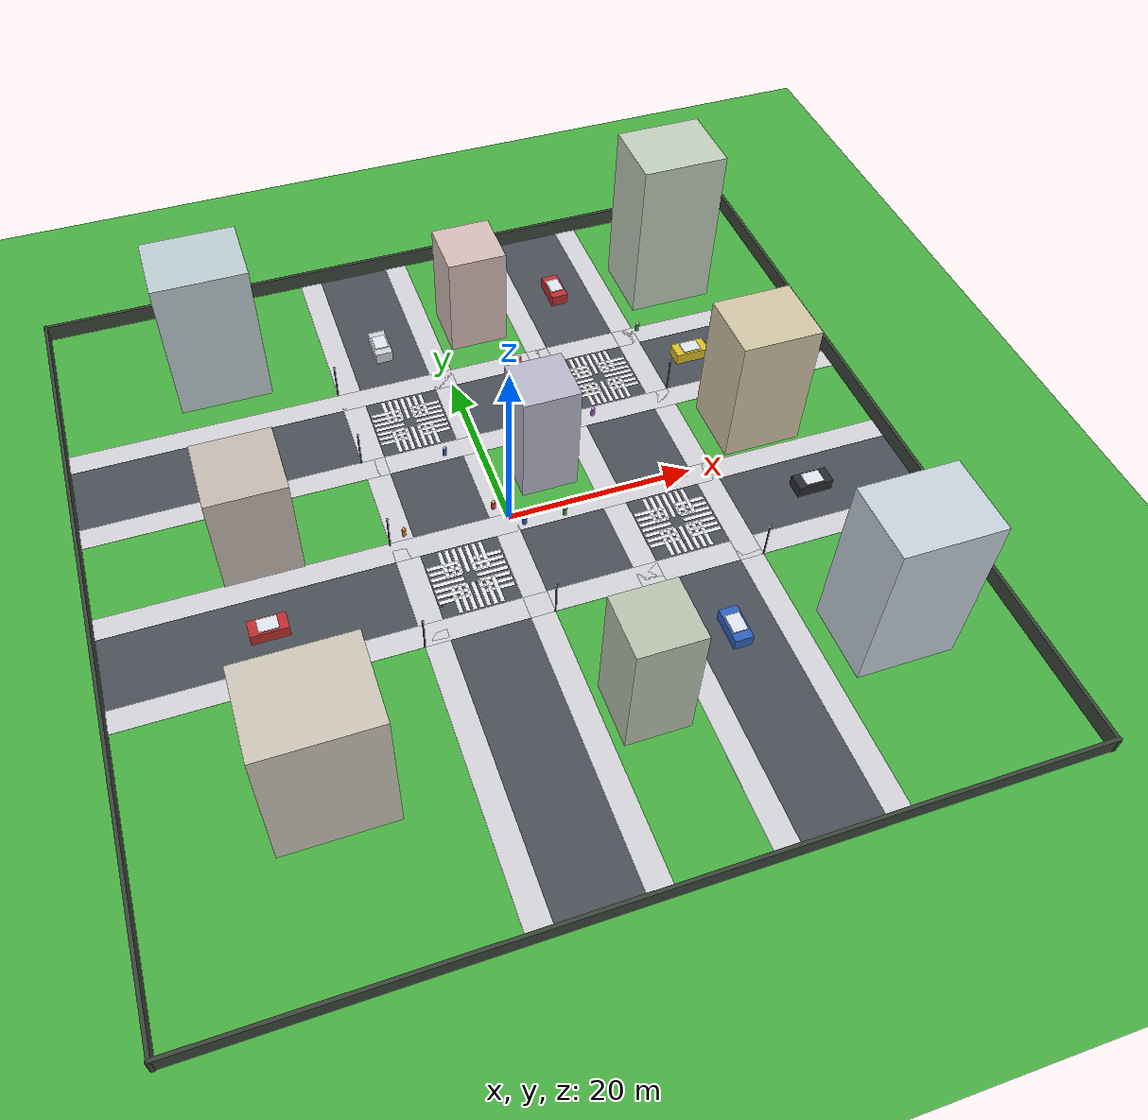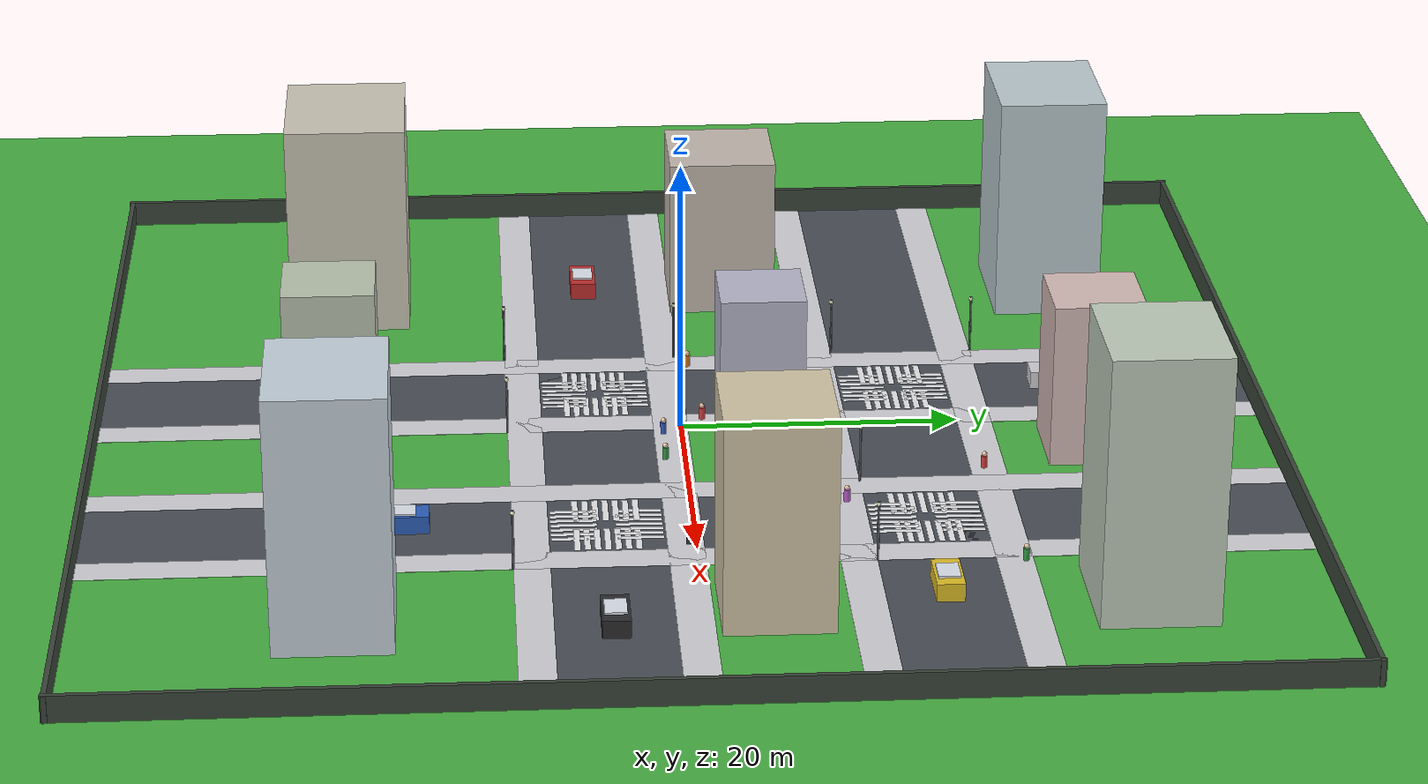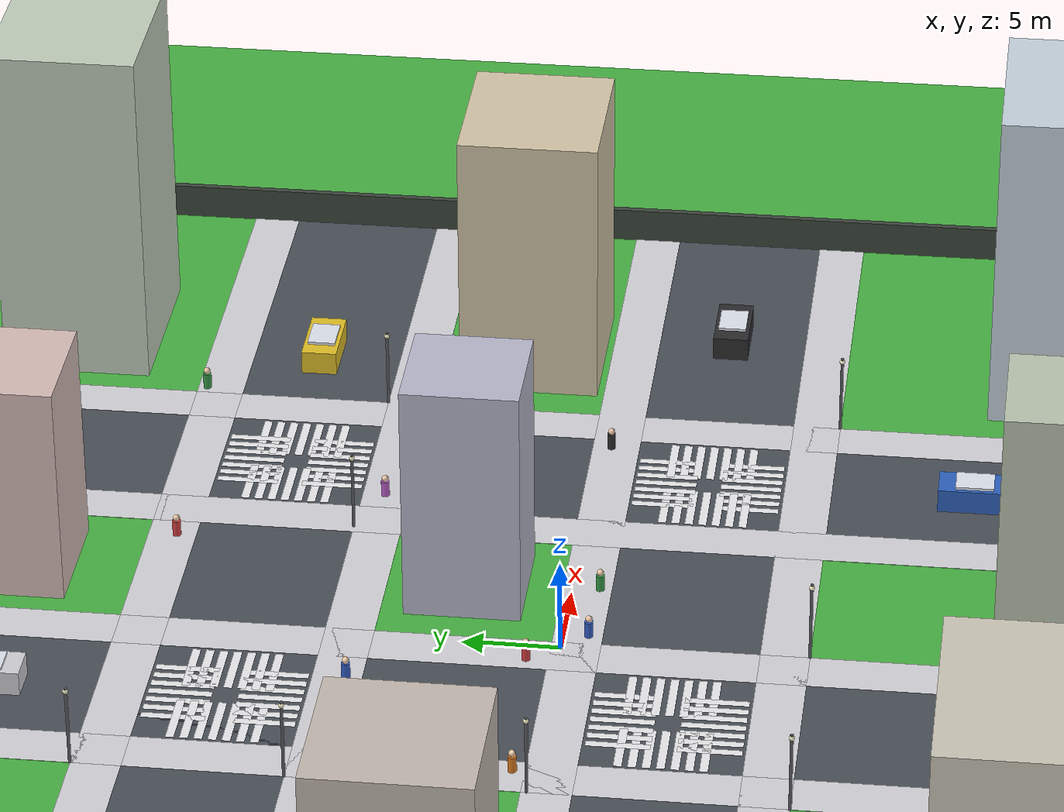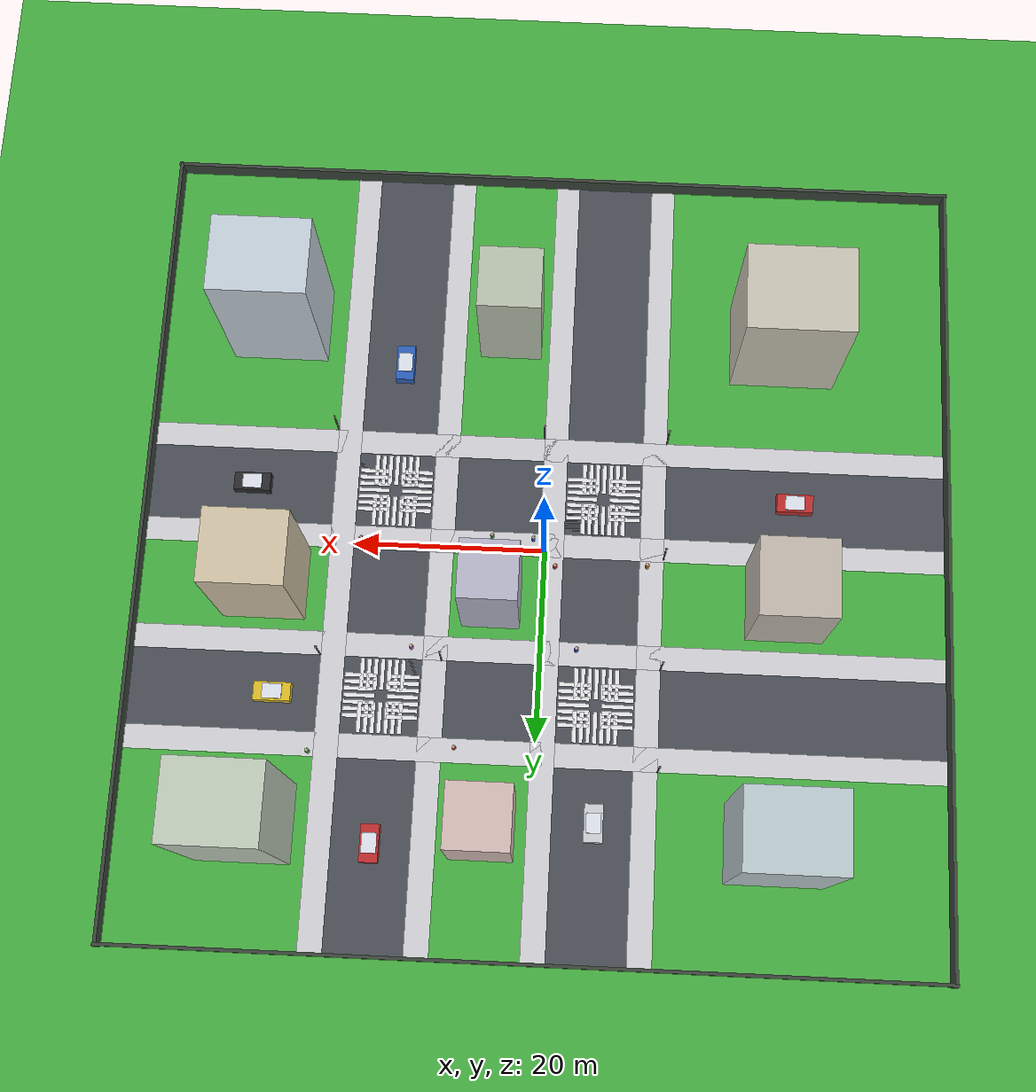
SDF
<?xml version="1.0"?>
<sdf version="1.9">
  <world name="city_second">
    <gravity>0 0 -9.81</gravity>
    <magnetic_field>6e-06 2.3e-05 -4.2e-05</magnetic_field>
    <physics name="1ms" type="ignored">
      <max_step_size>0.001</max_step_size>
      <real_time_factor>1.0</real_time_factor>
      <real_time_update_rate>1000</real_time_update_rate>
    </physics>

    <plugin filename="gz-sim-physics-system" name="gz::sim::systems::Physics"/>
    <plugin filename="gz-sim-user-commands-system" name="gz::sim::systems::UserCommands"/>
    <plugin filename="gz-sim-scene-broadcaster-system" name="gz::sim::systems::SceneBroadcaster"/>
    <plugin filename="gz-sim-sensors-system" name="gz::sim::systems::Sensors">
      <render_engine>ogre2</render_engine>
    </plugin>

    <scene>
      <ambient>0.78 0.78 0.78 1</ambient>
      <background>0.78 0.88 0.97 1</background>
      <shadows>true</shadows>
      <grid>false</grid>
    </scene>

    <light name="sun" type="directional">
      <cast_shadows>true</cast_shadows>
      <pose>0 0 40 0 0 0</pose>
      <diffuse>0.98 0.98 0.98 1</diffuse>
      <specular>0.20 0.20 0.20 1</specular>
      <attenuation>
        <range>1000</range>
        <constant>0.9</constant>
        <linear>0.01</linear>
        <quadratic>0.001</quadratic>
      </attenuation>
      <direction>-0.45 0.22 -0.87</direction>
    </light>

    <model name="ground_plane">
      <static>true</static>
      <link name="link">
        <collision name="collision">
          <geometry><plane><normal>0 0 1</normal><size>300 300</size></plane></geometry>
        </collision>
        <visual name="visual">
          <geometry><plane><normal>0 0 1</normal><size>300 300</size></plane></geometry>
          <material>
            <ambient>0.28 0.69 0.26 1</ambient>
            <diffuse>0.28 0.69 0.26 1</diffuse>
            <specular>0.03 0.03 0.03 1</specular>
          </material>
        </visual>
      </link>
    </model>

    <model name="road_h_1">
      <static>true</static>
      <pose>0 -6.0 0.01 0 0 0.0</pose>
      <link name="link">
        <collision name="collision">
          <geometry><box><size>84 8.0 0.02</size></box></geometry>
        </collision>
        <visual name="visual">
          <geometry><box><size>84 8.0 0.02</size></box></geometry>
          <material>
            <ambient>0.29 0.31 0.34 1</ambient>
            <diffuse>0.29 0.31 0.34 1</diffuse>
            <specular>0.03 0.03 0.03 1</specular>
          </material>
        </visual>
      </link>
    </model>
    <model name="road_h_2">
      <static>true</static>
      <pose>0 16.0 0.01 0 0 0.0</pose>
      <link name="link">
        <collision name="collision">
          <geometry><box><size>84 8.0 0.02</size></box></geometry>
        </collision>
        <visual name="visual">
          <geometry><box><size>84 8.0 0.02</size></box></geometry>
          <material>
            <ambient>0.29 0.31 0.34 1</ambient>
            <diffuse>0.29 0.31 0.34 1</diffuse>
            <specular>0.03 0.03 0.03 1</specular>
          </material>
        </visual>
      </link>
    </model>
    <model name="road_v_1">
      <static>true</static>
      <pose>-6.0 0 0.01 0 0 0.0</pose>
      <link name="link">
        <collision name="collision">
          <geometry><box><size>8.0 84 0.02</size></box></geometry>
        </collision>
        <visual name="visual">
          <geometry><box><size>8.0 84 0.02</size></box></geometry>
          <material>
            <ambient>0.29 0.31 0.34 1</ambient>
            <diffuse>0.29 0.31 0.34 1</diffuse>
            <specular>0.03 0.03 0.03 1</specular>
          </material>
        </visual>
      </link>
    </model>
    <model name="road_v_2">
      <static>true</static>
      <pose>16.0 0 0.01 0 0 0.0</pose>
      <link name="link">
        <collision name="collision">
          <geometry><box><size>8.0 84 0.02</size></box></geometry>
        </collision>
        <visual name="visual">
          <geometry><box><size>8.0 84 0.02</size></box></geometry>
          <material>
            <ambient>0.29 0.31 0.34 1</ambient>
            <diffuse>0.29 0.31 0.34 1</diffuse>
            <specular>0.03 0.03 0.03 1</specular>
          </material>
        </visual>
      </link>
    </model>
    <model name="sidewalk_h_1_south">
      <static>true</static>
      <pose>0 -11.25 0.015 0 0 0.0</pose>
      <link name="link">
        <collision name="collision">
          <geometry><box><size>84 2.5 0.02</size></box></geometry>
        </collision>
        <visual name="visual">
          <geometry><box><size>84 2.5 0.02</size></box></geometry>
          <material>
            <ambient>0.83 0.83 0.85 1</ambient>
            <diffuse>0.83 0.83 0.85 1</diffuse>
            <specular>0.03 0.03 0.03 1</specular>
          </material>
        </visual>
      </link>
    </model>
    <model name="sidewalk_h_1_north">
      <static>true</static>
      <pose>0 -0.75 0.015 0 0 0.0</pose>
      <link name="link">
        <collision name="collision">
          <geometry><box><size>84 2.5 0.02</size></box></geometry>
        </collision>
        <visual name="visual">
          <geometry><box><size>84 2.5 0.02</size></box></geometry>
          <material>
            <ambient>0.83 0.83 0.85 1</ambient>
            <diffuse>0.83 0.83 0.85 1</diffuse>
            <specular>0.03 0.03 0.03 1</specular>
          </material>
        </visual>
      </link>
    </model>
    <model name="sidewalk_h_2_south">
      <static>true</static>
      <pose>0 10.75 0.015 0 0 0.0</pose>
      <link name="link">
        <collision name="collision">
          <geometry><box><size>84 2.5 0.02</size></box></geometry>
        </collision>
        <visual name="visual">
          <geometry><box><size>84 2.5 0.02</size></box></geometry>
          <material>
            <ambient>0.83 0.83 0.85 1</ambient>
            <diffuse>0.83 0.83 0.85 1</diffuse>
            <specular>0.03 0.03 0.03 1</specular>
          </material>
        </visual>
      </link>
    </model>
    <model name="sidewalk_h_2_north">
      <static>true</static>
      <pose>0 21.25 0.015 0 0 0.0</pose>
      <link name="link">
        <collision name="collision">
          <geometry><box><size>84 2.5 0.02</size></box></geometry>
        </collision>
        <visual name="visual">
          <geometry><box><size>84 2.5 0.02</size></box></geometry>
          <material>
            <ambient>0.83 0.83 0.85 1</ambient>
            <diffuse>0.83 0.83 0.85 1</diffuse>
            <specular>0.03 0.03 0.03 1</specular>
          </material>
        </visual>
      </link>
    </model>
    <model name="sidewalk_v_1_west">
      <static>true</static>
      <pose>-11.25 0 0.015 0 0 0.0</pose>
      <link name="link">
        <collision name="collision">
          <geometry><box><size>2.5 84 0.02</size></box></geometry>
        </collision>
        <visual name="visual">
          <geometry><box><size>2.5 84 0.02</size></box></geometry>
          <material>
            <ambient>0.83 0.83 0.85 1</ambient>
            <diffuse>0.83 0.83 0.85 1</diffuse>
            <specular>0.03 0.03 0.03 1</specular>
          </material>
        </visual>
      </link>
    </model>
    <model name="sidewalk_v_1_east">
      <static>true</static>
      <pose>-0.75 0 0.015 0 0 0.0</pose>
      <link name="link">
        <collision name="collision">
          <geometry><box><size>2.5 84 0.02</size></box></geometry>
        </collision>
        <visual name="visual">
          <geometry><box><size>2.5 84 0.02</size></box></geometry>
          <material>
            <ambient>0.83 0.83 0.85 1</ambient>
            <diffuse>0.83 0.83 0.85 1</diffuse>
            <specular>0.03 0.03 0.03 1</specular>
          </material>
        </visual>
      </link>
    </model>
    <model name="sidewalk_v_2_west">
      <static>true</static>
      <pose>10.75 0 0.015 0 0 0.0</pose>
      <link name="link">
        <collision name="collision">
          <geometry><box><size>2.5 84 0.02</size></box></geometry>
        </collision>
        <visual name="visual">
          <geometry><box><size>2.5 84 0.02</size></box></geometry>
          <material>
            <ambient>0.83 0.83 0.85 1</ambient>
            <diffuse>0.83 0.83 0.85 1</diffuse>
            <specular>0.03 0.03 0.03 1</specular>
          </material>
        </visual>
      </link>
    </model>
    <model name="sidewalk_v_2_east">
      <static>true</static>
      <pose>21.25 0 0.015 0 0 0.0</pose>
      <link name="link">
        <collision name="collision">
          <geometry><box><size>2.5 84 0.02</size></box></geometry>
        </collision>
        <visual name="visual">
          <geometry><box><size>2.5 84 0.02</size></box></geometry>
          <material>
            <ambient>0.83 0.83 0.85 1</ambient>
            <diffuse>0.83 0.83 0.85 1</diffuse>
            <specular>0.03 0.03 0.03 1</specular>
          </material>
        </visual>
      </link>
    </model>
    <model name="corner_sidewalk_1_1_1">
      <static>true</static>
      <pose>-11.25 -11.25 0.015 0 0 0.0</pose>
      <link name="link">
        <collision name="collision">
          <geometry><box><size>2.5 2.5 0.02</size></box></geometry>
        </collision>
        <visual name="visual">
          <geometry><box><size>2.5 2.5 0.02</size></box></geometry>
          <material>
            <ambient>0.83 0.83 0.85 1</ambient>
            <diffuse>0.83 0.83 0.85 1</diffuse>
            <specular>0.03 0.03 0.03 1</specular>
          </material>
        </visual>
      </link>
    </model>
    <model name="corner_sidewalk_1_1_2">
      <static>true</static>
      <pose>-11.25 -0.75 0.015 0 0 0.0</pose>
      <link name="link">
        <collision name="collision">
          <geometry><box><size>2.5 2.5 0.02</size></box></geometry>
        </collision>
        <visual name="visual">
          <geometry><box><size>2.5 2.5 0.02</size></box></geometry>
          <material>
            <ambient>0.83 0.83 0.85 1</ambient>
            <diffuse>0.83 0.83 0.85 1</diffuse>
            <specular>0.03 0.03 0.03 1</specular>
          </material>
        </visual>
      </link>
    </model>
    <model name="corner_sidewalk_1_1_3">
      <static>true</static>
      <pose>-0.75 -11.25 0.015 0 0 0.0</pose>
      <link name="link">
        <collision name="collision">
          <geometry><box><size>2.5 2.5 0.02</size></box></geometry>
        </collision>
        <visual name="visual">
          <geometry><box><size>2.5 2.5 0.02</size></box></geometry>
          <material>
            <ambient>0.83 0.83 0.85 1</ambient>
            <diffuse>0.83 0.83 0.85 1</diffuse>
            <specular>0.03 0.03 0.03 1</specular>
          </material>
        </visual>
      </link>
    </model>
    <model name="corner_sidewalk_1_1_4">
      <static>true</static>
      <pose>-0.75 -0.75 0.015 0 0 0.0</pose>
      <link name="link">
        <collision name="collision">
          <geometry><box><size>2.5 2.5 0.02</size></box></geometry>
        </collision>
        <visual name="visual">
          <geometry><box><size>2.5 2.5 0.02</size></box></geometry>
          <material>
            <ambient>0.83 0.83 0.85 1</ambient>
            <diffuse>0.83 0.83 0.85 1</diffuse>
            <specular>0.03 0.03 0.03 1</specular>
          </material>
        </visual>
      </link>
    </model>
    <model name="corner_sidewalk_1_2_1">
      <static>true</static>
      <pose>-11.25 10.75 0.015 0 0 0.0</pose>
      <link name="link">
        <collision name="collision">
          <geometry><box><size>2.5 2.5 0.02</size></box></geometry>
        </collision>
        <visual name="visual">
          <geometry><box><size>2.5 2.5 0.02</size></box></geometry>
          <material>
            <ambient>0.83 0.83 0.85 1</ambient>
            <diffuse>0.83 0.83 0.85 1</diffuse>
            <specular>0.03 0.03 0.03 1</specular>
          </material>
        </visual>
      </link>
    </model>
    <model name="corner_sidewalk_1_2_2">
      <static>true</static>
      <pose>-11.25 21.25 0.015 0 0 0.0</pose>
      <link name="link">
        <collision name="collision">
          <geometry><box><size>2.5 2.5 0.02</size></box></geometry>
        </collision>
        <visual name="visual">
          <geometry><box><size>2.5 2.5 0.02</size></box></geometry>
          <material>
            <ambient>0.83 0.83 0.85 1</ambient>
            <diffuse>0.83 0.83 0.85 1</diffuse>
            <specular>0.03 0.03 0.03 1</specular>
          </material>
        </visual>
      </link>
    </model>
    <model name="corner_sidewalk_1_2_3">
      <static>true</static>
      <pose>-0.75 10.75 0.015 0 0 0.0</pose>
      <link name="link">
        <collision name="collision">
          <geometry><box><size>2.5 2.5 0.02</size></box></geometry>
        </collision>
        <visual name="visual">
          <geometry><box><size>2.5 2.5 0.02</size></box></geometry>
          <material>
            <ambient>0.83 0.83 0.85 1</ambient>
            <diffuse>0.83 0.83 0.85 1</diffuse>
            <specular>0.03 0.03 0.03 1</specular>
          </material>
        </visual>
      </link>
    </model>
    <model name="corner_sidewalk_1_2_4">
      <static>true</static>
      <pose>-0.75 21.25 0.015 0 0 0.0</pose>
      <link name="link">
        <collision name="collision">
          <geometry><box><size>2.5 2.5 0.02</size></box></geometry>
        </collision>
        <visual name="visual">
          <geometry><box><size>2.5 2.5 0.02</size></box></geometry>
          <material>
            <ambient>0.83 0.83 0.85 1</ambient>
            <diffuse>0.83 0.83 0.85 1</diffuse>
            <specular>0.03 0.03 0.03 1</specular>
          </material>
        </visual>
      </link>
    </model>
    <model name="corner_sidewalk_2_1_1">
      <static>true</static>
      <pose>10.75 -11.25 0.015 0 0 0.0</pose>
      <link name="link">
        <collision name="collision">
          <geometry><box><size>2.5 2.5 0.02</size></box></geometry>
        </collision>
        <visual name="visual">
          <geometry><box><size>2.5 2.5 0.02</size></box></geometry>
          <material>
            <ambient>0.83 0.83 0.85 1</ambient>
            <diffuse>0.83 0.83 0.85 1</diffuse>
            <specular>0.03 0.03 0.03 1</specular>
          </material>
        </visual>
      </link>
    </model>
    <model name="corner_sidewalk_2_1_2">
      <static>true</static>
      <pose>10.75 -0.75 0.015 0 0 0.0</pose>
      <link name="link">
        <collision name="collision">
          <geometry><box><size>2.5 2.5 0.02</size></box></geometry>
        </collision>
        <visual name="visual">
          <geometry><box><size>2.5 2.5 0.02</size></box></geometry>
          <material>
            <ambient>0.83 0.83 0.85 1</ambient>
            <diffuse>0.83 0.83 0.85 1</diffuse>
            <specular>0.03 0.03 0.03 1</specular>
          </material>
        </visual>
      </link>
    </model>
    <model name="corner_sidewalk_2_1_3">
      <static>true</static>
      <pose>21.25 -11.25 0.015 0 0 0.0</pose>
      <link name="link">
        <collision name="collision">
          <geometry><box><size>2.5 2.5 0.02</size></box></geometry>
        </collision>
        <visual name="visual">
          <geometry><box><size>2.5 2.5 0.02</size></box></geometry>
          <material>
            <ambient>0.83 0.83 0.85 1</ambient>
            <diffuse>0.83 0.83 0.85 1</diffuse>
            <specular>0.03 0.03 0.03 1</specular>
          </material>
        </visual>
      </link>
    </model>
    <model name="corner_sidewalk_2_1_4">
      <static>true</static>
      <pose>21.25 -0.75 0.015 0 0 0.0</pose>
      <link name="link">
        <collision name="collision">
          <geometry><box><size>2.5 2.5 0.02</size></box></geometry>
        </collision>
        <visual name="visual">
          <geometry><box><size>2.5 2.5 0.02</size></box></geometry>
          <material>
            <ambient>0.83 0.83 0.85 1</ambient>
            <diffuse>0.83 0.83 0.85 1</diffuse>
            <specular>0.03 0.03 0.03 1</specular>
          </material>
        </visual>
      </link>
    </model>
    <model name="corner_sidewalk_2_2_1">
      <static>true</static>
      <pose>10.75 10.75 0.015 0 0 0.0</pose>
      <link name="link">
        <collision name="collision">
          <geometry><box><size>2.5 2.5 0.02</size></box></geometry>
        </collision>
        <visual name="visual">
          <geometry><box><size>2.5 2.5 0.02</size></box></geometry>
          <material>
            <ambient>0.83 0.83 0.85 1</ambient>
            <diffuse>0.83 0.83 0.85 1</diffuse>
            <specular>0.03 0.03 0.03 1</specular>
          </material>
        </visual>
      </link>
    </model>
    <model name="corner_sidewalk_2_2_2">
      <static>true</static>
      <pose>10.75 21.25 0.015 0 0 0.0</pose>
      <link name="link">
        <collision name="collision">
          <geometry><box><size>2.5 2.5 0.02</size></box></geometry>
        </collision>
        <visual name="visual">
          <geometry><box><size>2.5 2.5 0.02</size></box></geometry>
          <material>
            <ambient>0.83 0.83 0.85 1</ambient>
            <diffuse>0.83 0.83 0.85 1</diffuse>
            <specular>0.03 0.03 0.03 1</specular>
          </material>
        </visual>
      </link>
    </model>
    <model name="corner_sidewalk_2_2_3">
      <static>true</static>
      <pose>21.25 10.75 0.015 0 0 0.0</pose>
      <link name="link">
        <collision name="collision">
          <geometry><box><size>2.5 2.5 0.02</size></box></geometry>
        </collision>
        <visual name="visual">
          <geometry><box><size>2.5 2.5 0.02</size></box></geometry>
          <material>
            <ambient>0.83 0.83 0.85 1</ambient>
            <diffuse>0.83 0.83 0.85 1</diffuse>
            <specular>0.03 0.03 0.03 1</specular>
          </material>
        </visual>
      </link>
    </model>
    <model name="corner_sidewalk_2_2_4">
      <static>true</static>
      <pose>21.25 21.25 0.015 0 0 0.0</pose>
      <link name="link">
        <collision name="collision">
          <geometry><box><size>2.5 2.5 0.02</size></box></geometry>
        </collision>
        <visual name="visual">
          <geometry><box><size>2.5 2.5 0.02</size></box></geometry>
          <material>
            <ambient>0.83 0.83 0.85 1</ambient>
            <diffuse>0.83 0.83 0.85 1</diffuse>
            <specular>0.03 0.03 0.03 1</specular>
          </material>
        </visual>
      </link>
    </model>
    <model name="crosswalk_h_1_1_south_1">
      <static>true</static>
      <pose>-8.1 -8.25 0.017 0 0 0.0</pose>
      <link name="link">
        <collision name="collision">
          <geometry><box><size>0.42 3.2 0.01</size></box></geometry>
        </collision>
        <visual name="visual">
          <geometry><box><size>0.42 3.2 0.01</size></box></geometry>
          <material>
            <ambient>0.92 0.92 0.93 1</ambient>
            <diffuse>0.92 0.92 0.93 1</diffuse>
            <specular>0.03 0.03 0.03 1</specular>
          </material>
        </visual>
      </link>
    </model>
    <model name="crosswalk_h_1_1_south_2">
      <static>true</static>
      <pose>-7.3999999999999995 -8.25 0.017 0 0 0.0</pose>
      <link name="link">
        <collision name="collision">
          <geometry><box><size>0.42 3.2 0.01</size></box></geometry>
        </collision>
        <visual name="visual">
          <geometry><box><size>0.42 3.2 0.01</size></box></geometry>
          <material>
            <ambient>0.92 0.92 0.93 1</ambient>
            <diffuse>0.92 0.92 0.93 1</diffuse>
            <specular>0.03 0.03 0.03 1</specular>
          </material>
        </visual>
      </link>
    </model>
    <model name="crosswalk_h_1_1_south_3">
      <static>true</static>
      <pose>-6.699999999999999 -8.25 0.017 0 0 0.0</pose>
      <link name="link">
        <collision name="collision">
          <geometry><box><size>0.42 3.2 0.01</size></box></geometry>
        </collision>
        <visual name="visual">
          <geometry><box><size>0.42 3.2 0.01</size></box></geometry>
          <material>
            <ambient>0.92 0.92 0.93 1</ambient>
            <diffuse>0.92 0.92 0.93 1</diffuse>
            <specular>0.03 0.03 0.03 1</specular>
          </material>
        </visual>
      </link>
    </model>
    <model name="crosswalk_h_1_1_south_4">
      <static>true</static>
      <pose>-6.0 -8.25 0.017 0 0 0.0</pose>
      <link name="link">
        <collision name="collision">
          <geometry><box><size>0.42 3.2 0.01</size></box></geometry>
        </collision>
        <visual name="visual">
          <geometry><box><size>0.42 3.2 0.01</size></box></geometry>
          <material>
            <ambient>0.92 0.92 0.93 1</ambient>
            <diffuse>0.92 0.92 0.93 1</diffuse>
            <specular>0.03 0.03 0.03 1</specular>
          </material>
        </visual>
      </link>
    </model>
    <model name="crosswalk_h_1_1_south_5">
      <static>true</static>
      <pose>-5.3 -8.25 0.017 0 0 0.0</pose>
      <link name="link">
        <collision name="collision">
          <geometry><box><size>0.42 3.2 0.01</size></box></geometry>
        </collision>
        <visual name="visual">
          <geometry><box><size>0.42 3.2 0.01</size></box></geometry>
          <material>
            <ambient>0.92 0.92 0.93 1</ambient>
            <diffuse>0.92 0.92 0.93 1</diffuse>
            <specular>0.03 0.03 0.03 1</specular>
          </material>
        </visual>
      </link>
    </model>
    <model name="crosswalk_h_1_1_south_6">
      <static>true</static>
      <pose>-4.6 -8.25 0.017 0 0 0.0</pose>
      <link name="link">
        <collision name="collision">
          <geometry><box><size>0.42 3.2 0.01</size></box></geometry>
        </collision>
        <visual name="visual">
          <geometry><box><size>0.42 3.2 0.01</size></box></geometry>
          <material>
            <ambient>0.92 0.92 0.93 1</ambient>
            <diffuse>0.92 0.92 0.93 1</diffuse>
            <specular>0.03 0.03 0.03 1</specular>
          </material>
        </visual>
      </link>
    </model>
    <model name="crosswalk_h_1_1_south_7">
      <static>true</static>
      <pose>-3.9000000000000004 -8.25 0.017 0 0 0.0</pose>
      <link name="link">
        <collision name="collision">
          <geometry><box><size>0.42 3.2 0.01</size></box></geometry>
        </collision>
        <visual name="visual">
          <geometry><box><size>0.42 3.2 0.01</size></box></geometry>
          <material>
            <ambient>0.92 0.92 0.93 1</ambient>
            <diffuse>0.92 0.92 0.93 1</diffuse>
            <specular>0.03 0.03 0.03 1</specular>
          </material>
        </visual>
      </link>
    </model>
    <model name="crosswalk_h_1_1_north_1">
      <static>true</static>
      <pose>-8.1 -3.75 0.017 0 0 0.0</pose>
      <link name="link">
        <collision name="collision">
          <geometry><box><size>0.42 3.2 0.01</size></box></geometry>
        </collision>
        <visual name="visual">
          <geometry><box><size>0.42 3.2 0.01</size></box></geometry>
          <material>
            <ambient>0.92 0.92 0.93 1</ambient>
            <diffuse>0.92 0.92 0.93 1</diffuse>
            <specular>0.03 0.03 0.03 1</specular>
          </material>
        </visual>
      </link>
    </model>
    <model name="crosswalk_h_1_1_north_2">
      <static>true</static>
      <pose>-7.3999999999999995 -3.75 0.017 0 0 0.0</pose>
      <link name="link">
        <collision name="collision">
          <geometry><box><size>0.42 3.2 0.01</size></box></geometry>
        </collision>
        <visual name="visual">
          <geometry><box><size>0.42 3.2 0.01</size></box></geometry>
          <material>
            <ambient>0.92 0.92 0.93 1</ambient>
            <diffuse>0.92 0.92 0.93 1</diffuse>
            <specular>0.03 0.03 0.03 1</specular>
          </material>
        </visual>
      </link>
    </model>
    <model name="crosswalk_h_1_1_north_3">
      <static>true</static>
      <pose>-6.699999999999999 -3.75 0.017 0 0 0.0</pose>
      <link name="link">
        <collision name="collision">
          <geometry><box><size>0.42 3.2 0.01</size></box></geometry>
        </collision>
        <visual name="visual">
          <geometry><box><size>0.42 3.2 0.01</size></box></geometry>
          <material>
            <ambient>0.92 0.92 0.93 1</ambient>
            <diffuse>0.92 0.92 0.93 1</diffuse>
            <specular>0.03 0.03 0.03 1</specular>
          </material>
        </visual>
      </link>
    </model>
    <model name="crosswalk_h_1_1_north_4">
      <static>true</static>
      <pose>-6.0 -3.75 0.017 0 0 0.0</pose>
      <link name="link">
        <collision name="collision">
          <geometry><box><size>0.42 3.2 0.01</size></box></geometry>
        </collision>
        <visual name="visual">
          <geometry><box><size>0.42 3.2 0.01</size></box></geometry>
          <material>
            <ambient>0.92 0.92 0.93 1</ambient>
            <diffuse>0.92 0.92 0.93 1</diffuse>
            <specular>0.03 0.03 0.03 1</specular>
          </material>
        </visual>
      </link>
    </model>
    <model name="crosswalk_h_1_1_north_5">
      <static>true</static>
      <pose>-5.3 -3.75 0.017 0 0 0.0</pose>
      <link name="link">
        <collision name="collision">
          <geometry><box><size>0.42 3.2 0.01</size></box></geometry>
        </collision>
        <visual name="visual">
          <geometry><box><size>0.42 3.2 0.01</size></box></geometry>
          <material>
            <ambient>0.92 0.92 0.93 1</ambient>
            <diffuse>0.92 0.92 0.93 1</diffuse>
            <specular>0.03 0.03 0.03 1</specular>
          </material>
        </visual>
      </link>
    </model>
    <model name="crosswalk_h_1_1_north_6">
      <static>true</static>
      <pose>-4.6 -3.75 0.017 0 0 0.0</pose>
      <link name="link">
        <collision name="collision">
          <geometry><box><size>0.42 3.2 0.01</size></box></geometry>
        </collision>
        <visual name="visual">
          <geometry><box><size>0.42 3.2 0.01</size></box></geometry>
          <material>
            <ambient>0.92 0.92 0.93 1</ambient>
            <diffuse>0.92 0.92 0.93 1</diffuse>
            <specular>0.03 0.03 0.03 1</specular>
          </material>
        </visual>
      </link>
    </model>
    <model name="crosswalk_h_1_1_north_7">
      <static>true</static>
      <pose>-3.9000000000000004 -3.75 0.017 0 0 0.0</pose>
      <link name="link">
        <collision name="collision">
          <geometry><box><size>0.42 3.2 0.01</size></box></geometry>
        </collision>
        <visual name="visual">
          <geometry><box><size>0.42 3.2 0.01</size></box></geometry>
          <material>
            <ambient>0.92 0.92 0.93 1</ambient>
            <diffuse>0.92 0.92 0.93 1</diffuse>
            <specular>0.03 0.03 0.03 1</specular>
          </material>
        </visual>
      </link>
    </model>
    <model name="crosswalk_v_1_1_west_1">
      <static>true</static>
      <pose>-8.25 -8.1 0.017 0 0 0.0</pose>
      <link name="link">
        <collision name="collision">
          <geometry><box><size>3.2 0.42 0.01</size></box></geometry>
        </collision>
        <visual name="visual">
          <geometry><box><size>3.2 0.42 0.01</size></box></geometry>
          <material>
            <ambient>0.92 0.92 0.93 1</ambient>
            <diffuse>0.92 0.92 0.93 1</diffuse>
            <specular>0.03 0.03 0.03 1</specular>
          </material>
        </visual>
      </link>
    </model>
    <model name="crosswalk_v_1_1_west_2">
      <static>true</static>
      <pose>-8.25 -7.3999999999999995 0.017 0 0 0.0</pose>
      <link name="link">
        <collision name="collision">
          <geometry><box><size>3.2 0.42 0.01</size></box></geometry>
        </collision>
        <visual name="visual">
          <geometry><box><size>3.2 0.42 0.01</size></box></geometry>
          <material>
            <ambient>0.92 0.92 0.93 1</ambient>
            <diffuse>0.92 0.92 0.93 1</diffuse>
            <specular>0.03 0.03 0.03 1</specular>
          </material>
        </visual>
      </link>
    </model>
    <model name="crosswalk_v_1_1_west_3">
      <static>true</static>
      <pose>-8.25 -6.699999999999999 0.017 0 0 0.0</pose>
      <link name="link">
        <collision name="collision">
          <geometry><box><size>3.2 0.42 0.01</size></box></geometry>
        </collision>
        <visual name="visual">
          <geometry><box><size>3.2 0.42 0.01</size></box></geometry>
          <material>
            <ambient>0.92 0.92 0.93 1</ambient>
            <diffuse>0.92 0.92 0.93 1</diffuse>
            <specular>0.03 0.03 0.03 1</specular>
          </material>
        </visual>
      </link>
    </model>
    <model name="crosswalk_v_1_1_west_4">
      <static>true</static>
      <pose>-8.25 -6.0 0.017 0 0 0.0</pose>
      <link name="link">
        <collision name="collision">
          <geometry><box><size>3.2 0.42 0.01</size></box></geometry>
        </collision>
        <visual name="visual">
          <geometry><box><size>3.2 0.42 0.01</size></box></geometry>
          <material>
            <ambient>0.92 0.92 0.93 1</ambient>
            <diffuse>0.92 0.92 0.93 1</diffuse>
            <specular>0.03 0.03 0.03 1</specular>
          </material>
        </visual>
      </link>
    </model>
    <model name="crosswalk_v_1_1_west_5">
      <static>true</static>
      <pose>-8.25 -5.3 0.017 0 0 0.0</pose>
      <link name="link">
        <collision name="collision">
          <geometry><box><size>3.2 0.42 0.01</size></box></geometry>
        </collision>
        <visual name="visual">
          <geometry><box><size>3.2 0.42 0.01</size></box></geometry>
          <material>
            <ambient>0.92 0.92 0.93 1</ambient>
            <diffuse>0.92 0.92 0.93 1</diffuse>
            <specular>0.03 0.03 0.03 1</specular>
          </material>
        </visual>
      </link>
    </model>
    <model name="crosswalk_v_1_1_west_6">
      <static>true</static>
      <pose>-8.25 -4.6 0.017 0 0 0.0</pose>
      <link name="link">
        <collision name="collision">
          <geometry><box><size>3.2 0.42 0.01</size></box></geometry>
        </collision>
        <visual name="visual">
          <geometry><box><size>3.2 0.42 0.01</size></box></geometry>
          <material>
            <ambient>0.92 0.92 0.93 1</ambient>
            <diffuse>0.92 0.92 0.93 1</diffuse>
            <specular>0.03 0.03 0.03 1</specular>
          </material>
        </visual>
      </link>
    </model>
    <model name="crosswalk_v_1_1_west_7">
      <static>true</static>
      <pose>-8.25 -3.9000000000000004 0.017 0 0 0.0</pose>
      <link name="link">
        <collision name="collision">
          <geometry><box><size>3.2 0.42 0.01</size></box></geometry>
        </collision>
        <visual name="visual">
          <geometry><box><size>3.2 0.42 0.01</size></box></geometry>
          <material>
            <ambient>0.92 0.92 0.93 1</ambient>
            <diffuse>0.92 0.92 0.93 1</diffuse>
            <specular>0.03 0.03 0.03 1</specular>
          </material>
        </visual>
      </link>
    </model>
    <model name="crosswalk_v_1_1_east_1">
      <static>true</static>
      <pose>-3.75 -8.1 0.017 0 0 0.0</pose>
      <link name="link">
        <collision name="collision">
          <geometry><box><size>3.2 0.42 0.01</size></box></geometry>
        </collision>
        <visual name="visual">
          <geometry><box><size>3.2 0.42 0.01</size></box></geometry>
          <material>
            <ambient>0.92 0.92 0.93 1</ambient>
            <diffuse>0.92 0.92 0.93 1</diffuse>
            <specular>0.03 0.03 0.03 1</specular>
          </material>
        </visual>
      </link>
    </model>
    <model name="crosswalk_v_1_1_east_2">
      <static>true</static>
      <pose>-3.75 -7.3999999999999995 0.017 0 0 0.0</pose>
      <link name="link">
        <collision name="collision">
          <geometry><box><size>3.2 0.42 0.01</size></box></geometry>
        </collision>
        <visual name="visual">
          <geometry><box><size>3.2 0.42 0.01</size></box></geometry>
          <material>
            <ambient>0.92 0.92 0.93 1</ambient>
            <diffuse>0.92 0.92 0.93 1</diffuse>
            <specular>0.03 0.03 0.03 1</specular>
          </material>
        </visual>
      </link>
    </model>
    <model name="crosswalk_v_1_1_east_3">
      <static>true</static>
      <pose>-3.75 -6.699999999999999 0.017 0 0 0.0</pose>
      <link name="link">
        <collision name="collision">
          <geometry><box><size>3.2 0.42 0.01</size></box></geometry>
        </collision>
        <visual name="visual">
          <geometry><box><size>3.2 0.42 0.01</size></box></geometry>
          <material>
            <ambient>0.92 0.92 0.93 1</ambient>
            <diffuse>0.92 0.92 0.93 1</diffuse>
            <specular>0.03 0.03 0.03 1</specular>
          </material>
        </visual>
      </link>
    </model>
    <model name="crosswalk_v_1_1_east_4">
      <static>true</static>
      <pose>-3.75 -6.0 0.017 0 0 0.0</pose>
      <link name="link">
        <collision name="collision">
          <geometry><box><size>3.2 0.42 0.01</size></box></geometry>
        </collision>
        <visual name="visual">
          <geometry><box><size>3.2 0.42 0.01</size></box></geometry>
          <material>
            <ambient>0.92 0.92 0.93 1</ambient>
            <diffuse>0.92 0.92 0.93 1</diffuse>
            <specular>0.03 0.03 0.03 1</specular>
          </material>
        </visual>
      </link>
    </model>
    <model name="crosswalk_v_1_1_east_5">
      <static>true</static>
      <pose>-3.75 -5.3 0.017 0 0 0.0</pose>
      <link name="link">
        <collision name="collision">
          <geometry><box><size>3.2 0.42 0.01</size></box></geometry>
        </collision>
        <visual name="visual">
          <geometry><box><size>3.2 0.42 0.01</size></box></geometry>
          <material>
            <ambient>0.92 0.92 0.93 1</ambient>
            <diffuse>0.92 0.92 0.93 1</diffuse>
            <specular>0.03 0.03 0.03 1</specular>
          </material>
        </visual>
      </link>
    </model>
    <model name="crosswalk_v_1_1_east_6">
      <static>true</static>
      <pose>-3.75 -4.6 0.017 0 0 0.0</pose>
      <link name="link">
        <collision name="collision">
          <geometry><box><size>3.2 0.42 0.01</size></box></geometry>
        </collision>
        <visual name="visual">
          <geometry><box><size>3.2 0.42 0.01</size></box></geometry>
          <material>
            <ambient>0.92 0.92 0.93 1</ambient>
            <diffuse>0.92 0.92 0.93 1</diffuse>
            <specular>0.03 0.03 0.03 1</specular>
          </material>
        </visual>
      </link>
    </model>
    <model name="crosswalk_v_1_1_east_7">
      <static>true</static>
      <pose>-3.75 -3.9000000000000004 0.017 0 0 0.0</pose>
      <link name="link">
        <collision name="collision">
          <geometry><box><size>3.2 0.42 0.01</size></box></geometry>
        </collision>
        <visual name="visual">
          <geometry><box><size>3.2 0.42 0.01</size></box></geometry>
          <material>
            <ambient>0.92 0.92 0.93 1</ambient>
            <diffuse>0.92 0.92 0.93 1</diffuse>
            <specular>0.03 0.03 0.03 1</specular>
          </material>
        </visual>
      </link>
    </model>
    <model name="crosswalk_h_1_2_south_1">
      <static>true</static>
      <pose>-8.1 13.75 0.017 0 0 0.0</pose>
      <link name="link">
        <collision name="collision">
          <geometry><box><size>0.42 3.2 0.01</size></box></geometry>
        </collision>
        <visual name="visual">
          <geometry><box><size>0.42 3.2 0.01</size></box></geometry>
          <material>
            <ambient>0.92 0.92 0.93 1</ambient>
            <diffuse>0.92 0.92 0.93 1</diffuse>
            <specular>0.03 0.03 0.03 1</specular>
          </material>
        </visual>
      </link>
    </model>
    <model name="crosswalk_h_1_2_south_2">
      <static>true</static>
      <pose>-7.3999999999999995 13.75 0.017 0 0 0.0</pose>
      <link name="link">
        <collision name="collision">
          <geometry><box><size>0.42 3.2 0.01</size></box></geometry>
        </collision>
        <visual name="visual">
          <geometry><box><size>0.42 3.2 0.01</size></box></geometry>
          <material>
            <ambient>0.92 0.92 0.93 1</ambient>
            <diffuse>0.92 0.92 0.93 1</diffuse>
            <specular>0.03 0.03 0.03 1</specular>
          </material>
        </visual>
      </link>
    </model>
    <model name="crosswalk_h_1_2_south_3">
      <static>true</static>
      <pose>-6.699999999999999 13.75 0.017 0 0 0.0</pose>
      <link name="link">
        <collision name="collision">
          <geometry><box><size>0.42 3.2 0.01</size></box></geometry>
        </collision>
        <visual name="visual">
          <geometry><box><size>0.42 3.2 0.01</size></box></geometry>
          <material>
            <ambient>0.92 0.92 0.93 1</ambient>
            <diffuse>0.92 0.92 0.93 1</diffuse>
            <specular>0.03 0.03 0.03 1</specular>
          </material>
        </visual>
      </link>
    </model>
    <model name="crosswalk_h_1_2_south_4">
      <static>true</static>
      <pose>-6.0 13.75 0.017 0 0 0.0</pose>
      <link name="link">
        <collision name="collision">
          <geometry><box><size>0.42 3.2 0.01</size></box></geometry>
        </collision>
        <visual name="visual">
          <geometry><box><size>0.42 3.2 0.01</size></box></geometry>
          <material>
            <ambient>0.92 0.92 0.93 1</ambient>
            <diffuse>0.92 0.92 0.93 1</diffuse>
            <specular>0.03 0.03 0.03 1</specular>
          </material>
        </visual>
      </link>
    </model>
    <model name="crosswalk_h_1_2_south_5">
      <static>true</static>
      <pose>-5.3 13.75 0.017 0 0 0.0</pose>
      <link name="link">
        <collision name="collision">
          <geometry><box><size>0.42 3.2 0.01</size></box></geometry>
        </collision>
        <visual name="visual">
          <geometry><box><size>0.42 3.2 0.01</size></box></geometry>
          <material>
            <ambient>0.92 0.92 0.93 1</ambient>
            <diffuse>0.92 0.92 0.93 1</diffuse>
            <specular>0.03 0.03 0.03 1</specular>
          </material>
        </visual>
      </link>
    </model>
    <model name="crosswalk_h_1_2_south_6">
      <static>true</static>
      <pose>-4.6 13.75 0.017 0 0 0.0</pose>
      <link name="link">
        <collision name="collision">
          <geometry><box><size>0.42 3.2 0.01</size></box></geometry>
        </collision>
        <visual name="visual">
          <geometry><box><size>0.42 3.2 0.01</size></box></geometry>
          <material>
            <ambient>0.92 0.92 0.93 1</ambient>
            <diffuse>0.92 0.92 0.93 1</diffuse>
            <specular>0.03 0.03 0.03 1</specular>
          </material>
        </visual>
      </link>
    </model>
    <model name="crosswalk_h_1_2_south_7">
      <static>true</static>
      <pose>-3.9000000000000004 13.75 0.017 0 0 0.0</pose>
      <link name="link">
        <collision name="collision">
          <geometry><box><size>0.42 3.2 0.01</size></box></geometry>
        </collision>
        <visual name="visual">
          <geometry><box><size>0.42 3.2 0.01</size></box></geometry>
          <material>
            <ambient>0.92 0.92 0.93 1</ambient>
            <diffuse>0.92 0.92 0.93 1</diffuse>
            <specular>0.03 0.03 0.03 1</specular>
          </material>
        </visual>
      </link>
    </model>
    <model name="crosswalk_h_1_2_north_1">
      <static>true</static>
      <pose>-8.1 18.25 0.017 0 0 0.0</pose>
      <link name="link">
        <collision name="collision">
          <geometry><box><size>0.42 3.2 0.01</size></box></geometry>
        </collision>
        <visual name="visual">
          <geometry><box><size>0.42 3.2 0.01</size></box></geometry>
          <material>
            <ambient>0.92 0.92 0.93 1</ambient>
            <diffuse>0.92 0.92 0.93 1</diffuse>
            <specular>0.03 0.03 0.03 1</specular>
          </material>
        </visual>
      </link>
    </model>
    <model name="crosswalk_h_1_2_north_2">
      <static>true</static>
      <pose>-7.3999999999999995 18.25 0.017 0 0 0.0</pose>
      <link name="link">
        <collision name="collision">
          <geometry><box><size>0.42 3.2 0.01</size></box></geometry>
        </collision>
        <visual name="visual">
          <geometry><box><size>0.42 3.2 0.01</size></box></geometry>
          <material>
            <ambient>0.92 0.92 0.93 1</ambient>
            <diffuse>0.92 0.92 0.93 1</diffuse>
            <specular>0.03 0.03 0.03 1</specular>
          </material>
        </visual>
      </link>
    </model>
    <model name="crosswalk_h_1_2_north_3">
      <static>true</static>
      <pose>-6.699999999999999 18.25 0.017 0 0 0.0</pose>
      <link name="link">
        <collision name="collision">
          <geometry><box><size>0.42 3.2 0.01</size></box></geometry>
        </collision>
        <visual name="visual">
          <geometry><box><size>0.42 3.2 0.01</size></box></geometry>
          <material>
            <ambient>0.92 0.92 0.93 1</ambient>
            <diffuse>0.92 0.92 0.93 1</diffuse>
            <specular>0.03 0.03 0.03 1</specular>
          </material>
        </visual>
      </link>
    </model>
    <model name="crosswalk_h_1_2_north_4">
      <static>true</static>
      <pose>-6.0 18.25 0.017 0 0 0.0</pose>
      <link name="link">
        <collision name="collision">
          <geometry><box><size>0.42 3.2 0.01</size></box></geometry>
        </collision>
        <visual name="visual">
          <geometry><box><size>0.42 3.2 0.01</size></box></geometry>
          <material>
            <ambient>0.92 0.92 0.93 1</ambient>
            <diffuse>0.92 0.92 0.93 1</diffuse>
            <specular>0.03 0.03 0.03 1</specular>
          </material>
        </visual>
      </link>
    </model>
    <model name="crosswalk_h_1_2_north_5">
      <static>true</static>
      <pose>-5.3 18.25 0.017 0 0 0.0</pose>
      <link name="link">
        <collision name="collision">
          <geometry><box><size>0.42 3.2 0.01</size></box></geometry>
        </collision>
        <visual name="visual">
          <geometry><box><size>0.42 3.2 0.01</size></box></geometry>
          <material>
            <ambient>0.92 0.92 0.93 1</ambient>
            <diffuse>0.92 0.92 0.93 1</diffuse>
            <specular>0.03 0.03 0.03 1</specular>
          </material>
        </visual>
      </link>
    </model>
    <model name="crosswalk_h_1_2_north_6">
      <static>true</static>
      <pose>-4.6 18.25 0.017 0 0 0.0</pose>
      <link name="link">
        <collision name="collision">
          <geometry><box><size>0.42 3.2 0.01</size></box></geometry>
        </collision>
        <visual name="visual">
          <geometry><box><size>0.42 3.2 0.01</size></box></geometry>
          <material>
            <ambient>0.92 0.92 0.93 1</ambient>
            <diffuse>0.92 0.92 0.93 1</diffuse>
            <specular>0.03 0.03 0.03 1</specular>
          </material>
        </visual>
      </link>
    </model>
    <model name="crosswalk_h_1_2_north_7">
      <static>true</static>
      <pose>-3.9000000000000004 18.25 0.017 0 0 0.0</pose>
      <link name="link">
        <collision name="collision">
          <geometry><box><size>0.42 3.2 0.01</size></box></geometry>
        </collision>
        <visual name="visual">
          <geometry><box><size>0.42 3.2 0.01</size></box></geometry>
          <material>
            <ambient>0.92 0.92 0.93 1</ambient>
            <diffuse>0.92 0.92 0.93 1</diffuse>
            <specular>0.03 0.03 0.03 1</specular>
          </material>
        </visual>
      </link>
    </model>
    <model name="crosswalk_v_1_2_west_1">
      <static>true</static>
      <pose>-8.25 13.9 0.017 0 0 0.0</pose>
      <link name="link">
        <collision name="collision">
          <geometry><box><size>3.2 0.42 0.01</size></box></geometry>
        </collision>
        <visual name="visual">
          <geometry><box><size>3.2 0.42 0.01</size></box></geometry>
          <material>
            <ambient>0.92 0.92 0.93 1</ambient>
            <diffuse>0.92 0.92 0.93 1</diffuse>
            <specular>0.03 0.03 0.03 1</specular>
          </material>
        </visual>
      </link>
    </model>
    <model name="crosswalk_v_1_2_west_2">
      <static>true</static>
      <pose>-8.25 14.6 0.017 0 0 0.0</pose>
      <link name="link">
        <collision name="collision">
          <geometry><box><size>3.2 0.42 0.01</size></box></geometry>
        </collision>
        <visual name="visual">
          <geometry><box><size>3.2 0.42 0.01</size></box></geometry>
          <material>
            <ambient>0.92 0.92 0.93 1</ambient>
            <diffuse>0.92 0.92 0.93 1</diffuse>
            <specular>0.03 0.03 0.03 1</specular>
          </material>
        </visual>
      </link>
    </model>
    <model name="crosswalk_v_1_2_west_3">
      <static>true</static>
      <pose>-8.25 15.3 0.017 0 0 0.0</pose>
      <link name="link">
        <collision name="collision">
          <geometry><box><size>3.2 0.42 0.01</size></box></geometry>
        </collision>
        <visual name="visual">
          <geometry><box><size>3.2 0.42 0.01</size></box></geometry>
          <material>
            <ambient>0.92 0.92 0.93 1</ambient>
            <diffuse>0.92 0.92 0.93 1</diffuse>
            <specular>0.03 0.03 0.03 1</specular>
          </material>
        </visual>
      </link>
    </model>
    <model name="crosswalk_v_1_2_west_4">
      <static>true</static>
      <pose>-8.25 16.0 0.017 0 0 0.0</pose>
      <link name="link">
        <collision name="collision">
          <geometry><box><size>3.2 0.42 0.01</size></box></geometry>
        </collision>
        <visual name="visual">
          <geometry><box><size>3.2 0.42 0.01</size></box></geometry>
          <material>
            <ambient>0.92 0.92 0.93 1</ambient>
            <diffuse>0.92 0.92 0.93 1</diffuse>
            <specular>0.03 0.03 0.03 1</specular>
          </material>
        </visual>
      </link>
    </model>
    <model name="crosswalk_v_1_2_west_5">
      <static>true</static>
      <pose>-8.25 16.7 0.017 0 0 0.0</pose>
      <link name="link">
        <collision name="collision">
          <geometry><box><size>3.2 0.42 0.01</size></box></geometry>
        </collision>
        <visual name="visual">
          <geometry><box><size>3.2 0.42 0.01</size></box></geometry>
          <material>
            <ambient>0.92 0.92 0.93 1</ambient>
            <diffuse>0.92 0.92 0.93 1</diffuse>
            <specular>0.03 0.03 0.03 1</specular>
          </material>
        </visual>
      </link>
    </model>
    <model name="crosswalk_v_1_2_west_6">
      <static>true</static>
      <pose>-8.25 17.4 0.017 0 0 0.0</pose>
      <link name="link">
        <collision name="collision">
          <geometry><box><size>3.2 0.42 0.01</size></box></geometry>
        </collision>
        <visual name="visual">
          <geometry><box><size>3.2 0.42 0.01</size></box></geometry>
          <material>
            <ambient>0.92 0.92 0.93 1</ambient>
            <diffuse>0.92 0.92 0.93 1</diffuse>
            <specular>0.03 0.03 0.03 1</specular>
          </material>
        </visual>
      </link>
    </model>
    <model name="crosswalk_v_1_2_west_7">
      <static>true</static>
      <pose>-8.25 18.1 0.017 0 0 0.0</pose>
      <link name="link">
        <collision name="collision">
          <geometry><box><size>3.2 0.42 0.01</size></box></geometry>
        </collision>
        <visual name="visual">
          <geometry><box><size>3.2 0.42 0.01</size></box></geometry>
          <material>
            <ambient>0.92 0.92 0.93 1</ambient>
            <diffuse>0.92 0.92 0.93 1</diffuse>
            <specular>0.03 0.03 0.03 1</specular>
          </material>
        </visual>
      </link>
    </model>
    <model name="crosswalk_v_1_2_east_1">
      <static>true</static>
      <pose>-3.75 13.9 0.017 0 0 0.0</pose>
      <link name="link">
        <collision name="collision">
          <geometry><box><size>3.2 0.42 0.01</size></box></geometry>
        </collision>
        <visual name="visual">
          <geometry><box><size>3.2 0.42 0.01</size></box></geometry>
          <material>
            <ambient>0.92 0.92 0.93 1</ambient>
            <diffuse>0.92 0.92 0.93 1</diffuse>
            <specular>0.03 0.03 0.03 1</specular>
          </material>
        </visual>
      </link>
    </model>
    <model name="crosswalk_v_1_2_east_2">
      <static>true</static>
      <pose>-3.75 14.6 0.017 0 0 0.0</pose>
      <link name="link">
        <collision name="collision">
          <geometry><box><size>3.2 0.42 0.01</size></box></geometry>
        </collision>
        <visual name="visual">
          <geometry><box><size>3.2 0.42 0.01</size></box></geometry>
          <material>
            <ambient>0.92 0.92 0.93 1</ambient>
            <diffuse>0.92 0.92 0.93 1</diffuse>
            <specular>0.03 0.03 0.03 1</specular>
          </material>
        </visual>
      </link>
    </model>
    <model name="crosswalk_v_1_2_east_3">
      <static>true</static>
      <pose>-3.75 15.3 0.017 0 0 0.0</pose>
      <link name="link">
        <collision name="collision">
          <geometry><box><size>3.2 0.42 0.01</size></box></geometry>
        </collision>
        <visual name="visual">
          <geometry><box><size>3.2 0.42 0.01</size></box></geometry>
          <material>
            <ambient>0.92 0.92 0.93 1</ambient>
            <diffuse>0.92 0.92 0.93 1</diffuse>
            <specular>0.03 0.03 0.03 1</specular>
          </material>
        </visual>
      </link>
    </model>
    <model name="crosswalk_v_1_2_east_4">
      <static>true</static>
      <pose>-3.75 16.0 0.017 0 0 0.0</pose>
      <link name="link">
        <collision name="collision">
          <geometry><box><size>3.2 0.42 0.01</size></box></geometry>
        </collision>
        <visual name="visual">
          <geometry><box><size>3.2 0.42 0.01</size></box></geometry>
          <material>
            <ambient>0.92 0.92 0.93 1</ambient>
            <diffuse>0.92 0.92 0.93 1</diffuse>
            <specular>0.03 0.03 0.03 1</specular>
          </material>
        </visual>
      </link>
    </model>
    <model name="crosswalk_v_1_2_east_5">
      <static>true</static>
      <pose>-3.75 16.7 0.017 0 0 0.0</pose>
      <link name="link">
        <collision name="collision">
          <geometry><box><size>3.2 0.42 0.01</size></box></geometry>
        </collision>
        <visual name="visual">
          <geometry><box><size>3.2 0.42 0.01</size></box></geometry>
          <material>
            <ambient>0.92 0.92 0.93 1</ambient>
            <diffuse>0.92 0.92 0.93 1</diffuse>
            <specular>0.03 0.03 0.03 1</specular>
          </material>
        </visual>
      </link>
    </model>
    <model name="crosswalk_v_1_2_east_6">
      <static>true</static>
      <pose>-3.75 17.4 0.017 0 0 0.0</pose>
      <link name="link">
        <collision name="collision">
          <geometry><box><size>3.2 0.42 0.01</size></box></geometry>
        </collision>
        <visual name="visual">
          <geometry><box><size>3.2 0.42 0.01</size></box></geometry>
          <material>
            <ambient>0.92 0.92 0.93 1</ambient>
            <diffuse>0.92 0.92 0.93 1</diffuse>
            <specular>0.03 0.03 0.03 1</specular>
          </material>
        </visual>
      </link>
    </model>
    <model name="crosswalk_v_1_2_east_7">
      <static>true</static>
      <pose>-3.75 18.1 0.017 0 0 0.0</pose>
      <link name="link">
        <collision name="collision">
          <geometry><box><size>3.2 0.42 0.01</size></box></geometry>
        </collision>
        <visual name="visual">
          <geometry><box><size>3.2 0.42 0.01</size></box></geometry>
          <material>
            <ambient>0.92 0.92 0.93 1</ambient>
            <diffuse>0.92 0.92 0.93 1</diffuse>
            <specular>0.03 0.03 0.03 1</specular>
          </material>
        </visual>
      </link>
    </model>
    <model name="crosswalk_h_2_1_south_1">
      <static>true</static>
      <pose>13.9 -8.25 0.017 0 0 0.0</pose>
      <link name="link">
        <collision name="collision">
          <geometry><box><size>0.42 3.2 0.01</size></box></geometry>
        </collision>
        <visual name="visual">
          <geometry><box><size>0.42 3.2 0.01</size></box></geometry>
          <material>
            <ambient>0.92 0.92 0.93 1</ambient>
            <diffuse>0.92 0.92 0.93 1</diffuse>
            <specular>0.03 0.03 0.03 1</specular>
          </material>
        </visual>
      </link>
    </model>
    <model name="crosswalk_h_2_1_south_2">
      <static>true</static>
      <pose>14.6 -8.25 0.017 0 0 0.0</pose>
      <link name="link">
        <collision name="collision">
          <geometry><box><size>0.42 3.2 0.01</size></box></geometry>
        </collision>
        <visual name="visual">
          <geometry><box><size>0.42 3.2 0.01</size></box></geometry>
          <material>
            <ambient>0.92 0.92 0.93 1</ambient>
            <diffuse>0.92 0.92 0.93 1</diffuse>
            <specular>0.03 0.03 0.03 1</specular>
          </material>
        </visual>
      </link>
    </model>
    <model name="crosswalk_h_2_1_south_3">
      <static>true</static>
      <pose>15.3 -8.25 0.017 0 0 0.0</pose>
      <link name="link">
        <collision name="collision">
          <geometry><box><size>0.42 3.2 0.01</size></box></geometry>
        </collision>
        <visual name="visual">
          <geometry><box><size>0.42 3.2 0.01</size></box></geometry>
          <material>
            <ambient>0.92 0.92 0.93 1</ambient>
            <diffuse>0.92 0.92 0.93 1</diffuse>
            <specular>0.03 0.03 0.03 1</specular>
          </material>
        </visual>
      </link>
    </model>
    <model name="crosswalk_h_2_1_south_4">
      <static>true</static>
      <pose>16.0 -8.25 0.017 0 0 0.0</pose>
      <link name="link">
        <collision name="collision">
          <geometry><box><size>0.42 3.2 0.01</size></box></geometry>
        </collision>
        <visual name="visual">
          <geometry><box><size>0.42 3.2 0.01</size></box></geometry>
          <material>
            <ambient>0.92 0.92 0.93 1</ambient>
            <diffuse>0.92 0.92 0.93 1</diffuse>
            <specular>0.03 0.03 0.03 1</specular>
          </material>
        </visual>
      </link>
    </model>
    <model name="crosswalk_h_2_1_south_5">
      <static>true</static>
      <pose>16.7 -8.25 0.017 0 0 0.0</pose>
      <link name="link">
        <collision name="collision">
          <geometry><box><size>0.42 3.2 0.01</size></box></geometry>
        </collision>
        <visual name="visual">
          <geometry><box><size>0.42 3.2 0.01</size></box></geometry>
          <material>
            <ambient>0.92 0.92 0.93 1</ambient>
            <diffuse>0.92 0.92 0.93 1</diffuse>
            <specular>0.03 0.03 0.03 1</specular>
          </material>
        </visual>
      </link>
    </model>
    <model name="crosswalk_h_2_1_south_6">
      <static>true</static>
      <pose>17.4 -8.25 0.017 0 0 0.0</pose>
      <link name="link">
        <collision name="collision">
          <geometry><box><size>0.42 3.2 0.01</size></box></geometry>
        </collision>
        <visual name="visual">
          <geometry><box><size>0.42 3.2 0.01</size></box></geometry>
          <material>
            <ambient>0.92 0.92 0.93 1</ambient>
            <diffuse>0.92 0.92 0.93 1</diffuse>
            <specular>0.03 0.03 0.03 1</specular>
          </material>
        </visual>
      </link>
    </model>
    <model name="crosswalk_h_2_1_south_7">
      <static>true</static>
      <pose>18.1 -8.25 0.017 0 0 0.0</pose>
      <link name="link">
        <collision name="collision">
          <geometry><box><size>0.42 3.2 0.01</size></box></geometry>
        </collision>
        <visual name="visual">
          <geometry><box><size>0.42 3.2 0.01</size></box></geometry>
          <material>
            <ambient>0.92 0.92 0.93 1</ambient>
            <diffuse>0.92 0.92 0.93 1</diffuse>
            <specular>0.03 0.03 0.03 1</specular>
          </material>
        </visual>
      </link>
    </model>
    <model name="crosswalk_h_2_1_north_1">
      <static>true</static>
      <pose>13.9 -3.75 0.017 0 0 0.0</pose>
      <link name="link">
        <collision name="collision">
          <geometry><box><size>0.42 3.2 0.01</size></box></geometry>
        </collision>
        <visual name="visual">
          <geometry><box><size>0.42 3.2 0.01</size></box></geometry>
          <material>
            <ambient>0.92 0.92 0.93 1</ambient>
            <diffuse>0.92 0.92 0.93 1</diffuse>
            <specular>0.03 0.03 0.03 1</specular>
          </material>
        </visual>
      </link>
    </model>
    <model name="crosswalk_h_2_1_north_2">
      <static>true</static>
      <pose>14.6 -3.75 0.017 0 0 0.0</pose>
      <link name="link">
        <collision name="collision">
          <geometry><box><size>0.42 3.2 0.01</size></box></geometry>
        </collision>
        <visual name="visual">
          <geometry><box><size>0.42 3.2 0.01</size></box></geometry>
          <material>
            <ambient>0.92 0.92 0.93 1</ambient>
            <diffuse>0.92 0.92 0.93 1</diffuse>
            <specular>0.03 0.03 0.03 1</specular>
          </material>
        </visual>
      </link>
    </model>
    <model name="crosswalk_h_2_1_north_3">
      <static>true</static>
      <pose>15.3 -3.75 0.017 0 0 0.0</pose>
      <link name="link">
        <collision name="collision">
          <geometry><box><size>0.42 3.2 0.01</size></box></geometry>
        </collision>
        <visual name="visual">
          <geometry><box><size>0.42 3.2 0.01</size></box></geometry>
          <material>
            <ambient>0.92 0.92 0.93 1</ambient>
            <diffuse>0.92 0.92 0.93 1</diffuse>
            <specular>0.03 0.03 0.03 1</specular>
          </material>
        </visual>
      </link>
    </model>
    <model name="crosswalk_h_2_1_north_4">
      <static>true</static>
      <pose>16.0 -3.75 0.017 0 0 0.0</pose>
      <link name="link">
        <collision name="collision">
          <geometry><box><size>0.42 3.2 0.01</size></box></geometry>
        </collision>
        <visual name="visual">
          <geometry><box><size>0.42 3.2 0.01</size></box></geometry>
          <material>
            <ambient>0.92 0.92 0.93 1</ambient>
            <diffuse>0.92 0.92 0.93 1</diffuse>
            <specular>0.03 0.03 0.03 1</specular>
          </material>
        </visual>
      </link>
    </model>
    <model name="crosswalk_h_2_1_north_5">
      <static>true</static>
      <pose>16.7 -3.75 0.017 0 0 0.0</pose>
      <link name="link">
        <collision name="collision">
          <geometry><box><size>0.42 3.2 0.01</size></box></geometry>
        </collision>
        <visual name="visual">
          <geometry><box><size>0.42 3.2 0.01</size></box></geometry>
          <material>
            <ambient>0.92 0.92 0.93 1</ambient>
            <diffuse>0.92 0.92 0.93 1</diffuse>
            <specular>0.03 0.03 0.03 1</specular>
          </material>
        </visual>
      </link>
    </model>
    <model name="crosswalk_h_2_1_north_6">
      <static>true</static>
      <pose>17.4 -3.75 0.017 0 0 0.0</pose>
      <link name="link">
        <collision name="collision">
          <geometry><box><size>0.42 3.2 0.01</size></box></geometry>
        </collision>
        <visual name="visual">
          <geometry><box><size>0.42 3.2 0.01</size></box></geometry>
          <material>
            <ambient>0.92 0.92 0.93 1</ambient>
            <diffuse>0.92 0.92 0.93 1</diffuse>
            <specular>0.03 0.03 0.03 1</specular>
          </material>
        </visual>
      </link>
    </model>
    <model name="crosswalk_h_2_1_north_7">
      <static>true</static>
      <pose>18.1 -3.75 0.017 0 0 0.0</pose>
      <link name="link">
        <collision name="collision">
          <geometry><box><size>0.42 3.2 0.01</size></box></geometry>
        </collision>
        <visual name="visual">
          <geometry><box><size>0.42 3.2 0.01</size></box></geometry>
          <material>
            <ambient>0.92 0.92 0.93 1</ambient>
            <diffuse>0.92 0.92 0.93 1</diffuse>
            <specular>0.03 0.03 0.03 1</specular>
          </material>
        </visual>
      </link>
    </model>
    <model name="crosswalk_v_2_1_west_1">
      <static>true</static>
      <pose>13.75 -8.1 0.017 0 0 0.0</pose>
      <link name="link">
        <collision name="collision">
          <geometry><box><size>3.2 0.42 0.01</size></box></geometry>
        </collision>
        <visual name="visual">
          <geometry><box><size>3.2 0.42 0.01</size></box></geometry>
          <material>
            <ambient>0.92 0.92 0.93 1</ambient>
            <diffuse>0.92 0.92 0.93 1</diffuse>
            <specular>0.03 0.03 0.03 1</specular>
          </material>
        </visual>
      </link>
    </model>
    <model name="crosswalk_v_2_1_west_2">
      <static>true</static>
      <pose>13.75 -7.3999999999999995 0.017 0 0 0.0</pose>
      <link name="link">
        <collision name="collision">
          <geometry><box><size>3.2 0.42 0.01</size></box></geometry>
        </collision>
        <visual name="visual">
          <geometry><box><size>3.2 0.42 0.01</size></box></geometry>
          <material>
            <ambient>0.92 0.92 0.93 1</ambient>
            <diffuse>0.92 0.92 0.93 1</diffuse>
            <specular>0.03 0.03 0.03 1</specular>
          </material>
        </visual>
      </link>
    </model>
    <model name="crosswalk_v_2_1_west_3">
      <static>true</static>
      <pose>13.75 -6.699999999999999 0.017 0 0 0.0</pose>
      <link name="link">
        <collision name="collision">
          <geometry><box><size>3.2 0.42 0.01</size></box></geometry>
        </collision>
        <visual name="visual">
          <geometry><box><size>3.2 0.42 0.01</size></box></geometry>
          <material>
            <ambient>0.92 0.92 0.93 1</ambient>
            <diffuse>0.92 0.92 0.93 1</diffuse>
            <specular>0.03 0.03 0.03 1</specular>
          </material>
        </visual>
      </link>
    </model>
    <model name="crosswalk_v_2_1_west_4">
      <static>true</static>
      <pose>13.75 -6.0 0.017 0 0 0.0</pose>
      <link name="link">
        <collision name="collision">
          <geometry><box><size>3.2 0.42 0.01</size></box></geometry>
        </collision>
        <visual name="visual">
          <geometry><box><size>3.2 0.42 0.01</size></box></geometry>
          <material>
            <ambient>0.92 0.92 0.93 1</ambient>
            <diffuse>0.92 0.92 0.93 1</diffuse>
            <specular>0.03 0.03 0.03 1</specular>
          </material>
        </visual>
      </link>
    </model>
    <model name="crosswalk_v_2_1_west_5">
      <static>true</static>
      <pose>13.75 -5.3 0.017 0 0 0.0</pose>
      <link name="link">
        <collision name="collision">
          <geometry><box><size>3.2 0.42 0.01</size></box></geometry>
        </collision>
        <visual name="visual">
          <geometry><box><size>3.2 0.42 0.01</size></box></geometry>
          <material>
            <ambient>0.92 0.92 0.93 1</ambient>
            <diffuse>0.92 0.92 0.93 1</diffuse>
            <specular>0.03 0.03 0.03 1</specular>
          </material>
        </visual>
      </link>
    </model>
    <model name="crosswalk_v_2_1_west_6">
      <static>true</static>
      <pose>13.75 -4.6 0.017 0 0 0.0</pose>
      <link name="link">
        <collision name="collision">
          <geometry><box><size>3.2 0.42 0.01</size></box></geometry>
        </collision>
        <visual name="visual">
          <geometry><box><size>3.2 0.42 0.01</size></box></geometry>
          <material>
            <ambient>0.92 0.92 0.93 1</ambient>
            <diffuse>0.92 0.92 0.93 1</diffuse>
            <specular>0.03 0.03 0.03 1</specular>
          </material>
        </visual>
      </link>
    </model>
    <model name="crosswalk_v_2_1_west_7">
      <static>true</static>
      <pose>13.75 -3.9000000000000004 0.017 0 0 0.0</pose>
      <link name="link">
        <collision name="collision">
          <geometry><box><size>3.2 0.42 0.01</size></box></geometry>
        </collision>
        <visual name="visual">
          <geometry><box><size>3.2 0.42 0.01</size></box></geometry>
          <material>
            <ambient>0.92 0.92 0.93 1</ambient>
            <diffuse>0.92 0.92 0.93 1</diffuse>
            <specular>0.03 0.03 0.03 1</specular>
          </material>
        </visual>
      </link>
    </model>
    <model name="crosswalk_v_2_1_east_1">
      <static>true</static>
      <pose>18.25 -8.1 0.017 0 0 0.0</pose>
      <link name="link">
        <collision name="collision">
          <geometry><box><size>3.2 0.42 0.01</size></box></geometry>
        </collision>
        <visual name="visual">
          <geometry><box><size>3.2 0.42 0.01</size></box></geometry>
          <material>
            <ambient>0.92 0.92 0.93 1</ambient>
            <diffuse>0.92 0.92 0.93 1</diffuse>
            <specular>0.03 0.03 0.03 1</specular>
          </material>
        </visual>
      </link>
    </model>
    <model name="crosswalk_v_2_1_east_2">
      <static>true</static>
      <pose>18.25 -7.3999999999999995 0.017 0 0 0.0</pose>
      <link name="link">
        <collision name="collision">
          <geometry><box><size>3.2 0.42 0.01</size></box></geometry>
        </collision>
        <visual name="visual">
          <geometry><box><size>3.2 0.42 0.01</size></box></geometry>
          <material>
            <ambient>0.92 0.92 0.93 1</ambient>
            <diffuse>0.92 0.92 0.93 1</diffuse>
            <specular>0.03 0.03 0.03 1</specular>
          </material>
        </visual>
      </link>
    </model>
    <model name="crosswalk_v_2_1_east_3">
      <static>true</static>
      <pose>18.25 -6.699999999999999 0.017 0 0 0.0</pose>
      <link name="link">
        <collision name="collision">
          <geometry><box><size>3.2 0.42 0.01</size></box></geometry>
        </collision>
        <visual name="visual">
          <geometry><box><size>3.2 0.42 0.01</size></box></geometry>
          <material>
            <ambient>0.92 0.92 0.93 1</ambient>
            <diffuse>0.92 0.92 0.93 1</diffuse>
            <specular>0.03 0.03 0.03 1</specular>
          </material>
        </visual>
      </link>
    </model>
    <model name="crosswalk_v_2_1_east_4">
      <static>true</static>
      <pose>18.25 -6.0 0.017 0 0 0.0</pose>
      <link name="link">
        <collision name="collision">
          <geometry><box><size>3.2 0.42 0.01</size></box></geometry>
        </collision>
        <visual name="visual">
          <geometry><box><size>3.2 0.42 0.01</size></box></geometry>
          <material>
            <ambient>0.92 0.92 0.93 1</ambient>
            <diffuse>0.92 0.92 0.93 1</diffuse>
            <specular>0.03 0.03 0.03 1</specular>
          </material>
        </visual>
      </link>
    </model>
    <model name="crosswalk_v_2_1_east_5">
      <static>true</static>
      <pose>18.25 -5.3 0.017 0 0 0.0</pose>
      <link name="link">
        <collision name="collision">
          <geometry><box><size>3.2 0.42 0.01</size></box></geometry>
        </collision>
        <visual name="visual">
          <geometry><box><size>3.2 0.42 0.01</size></box></geometry>
          <material>
            <ambient>0.92 0.92 0.93 1</ambient>
            <diffuse>0.92 0.92 0.93 1</diffuse>
            <specular>0.03 0.03 0.03 1</specular>
          </material>
        </visual>
      </link>
    </model>
    <model name="crosswalk_v_2_1_east_6">
      <static>true</static>
      <pose>18.25 -4.6 0.017 0 0 0.0</pose>
      <link name="link">
        <collision name="collision">
          <geometry><box><size>3.2 0.42 0.01</size></box></geometry>
        </collision>
        <visual name="visual">
          <geometry><box><size>3.2 0.42 0.01</size></box></geometry>
          <material>
            <ambient>0.92 0.92 0.93 1</ambient>
            <diffuse>0.92 0.92 0.93 1</diffuse>
            <specular>0.03 0.03 0.03 1</specular>
          </material>
        </visual>
      </link>
    </model>
    <model name="crosswalk_v_2_1_east_7">
      <static>true</static>
      <pose>18.25 -3.9000000000000004 0.017 0 0 0.0</pose>
      <link name="link">
        <collision name="collision">
          <geometry><box><size>3.2 0.42 0.01</size></box></geometry>
        </collision>
        <visual name="visual">
          <geometry><box><size>3.2 0.42 0.01</size></box></geometry>
          <material>
            <ambient>0.92 0.92 0.93 1</ambient>
            <diffuse>0.92 0.92 0.93 1</diffuse>
            <specular>0.03 0.03 0.03 1</specular>
          </material>
        </visual>
      </link>
    </model>
    <model name="crosswalk_h_2_2_south_1">
      <static>true</static>
      <pose>13.9 13.75 0.017 0 0 0.0</pose>
      <link name="link">
        <collision name="collision">
          <geometry><box><size>0.42 3.2 0.01</size></box></geometry>
        </collision>
        <visual name="visual">
          <geometry><box><size>0.42 3.2 0.01</size></box></geometry>
          <material>
            <ambient>0.92 0.92 0.93 1</ambient>
            <diffuse>0.92 0.92 0.93 1</diffuse>
            <specular>0.03 0.03 0.03 1</specular>
          </material>
        </visual>
      </link>
    </model>
    <model name="crosswalk_h_2_2_south_2">
      <static>true</static>
      <pose>14.6 13.75 0.017 0 0 0.0</pose>
      <link name="link">
        <collision name="collision">
          <geometry><box><size>0.42 3.2 0.01</size></box></geometry>
        </collision>
        <visual name="visual">
          <geometry><box><size>0.42 3.2 0.01</size></box></geometry>
          <material>
            <ambient>0.92 0.92 0.93 1</ambient>
            <diffuse>0.92 0.92 0.93 1</diffuse>
            <specular>0.03 0.03 0.03 1</specular>
          </material>
        </visual>
      </link>
    </model>
    <model name="crosswalk_h_2_2_south_3">
      <static>true</static>
      <pose>15.3 13.75 0.017 0 0 0.0</pose>
      <link name="link">
        <collision name="collision">
          <geometry><box><size>0.42 3.2 0.01</size></box></geometry>
        </collision>
        <visual name="visual">
          <geometry><box><size>0.42 3.2 0.01</size></box></geometry>
          <material>
            <ambient>0.92 0.92 0.93 1</ambient>
            <diffuse>0.92 0.92 0.93 1</diffuse>
            <specular>0.03 0.03 0.03 1</specular>
          </material>
        </visual>
      </link>
    </model>
    <model name="crosswalk_h_2_2_south_4">
      <static>true</static>
      <pose>16.0 13.75 0.017 0 0 0.0</pose>
      <link name="link">
        <collision name="collision">
          <geometry><box><size>0.42 3.2 0.01</size></box></geometry>
        </collision>
        <visual name="visual">
          <geometry><box><size>0.42 3.2 0.01</size></box></geometry>
          <material>
            <ambient>0.92 0.92 0.93 1</ambient>
            <diffuse>0.92 0.92 0.93 1</diffuse>
            <specular>0.03 0.03 0.03 1</specular>
          </material>
        </visual>
      </link>
    </model>
    <model name="crosswalk_h_2_2_south_5">
      <static>true</static>
      <pose>16.7 13.75 0.017 0 0 0.0</pose>
      <link name="link">
        <collision name="collision">
          <geometry><box><size>0.42 3.2 0.01</size></box></geometry>
        </collision>
        <visual name="visual">
          <geometry><box><size>0.42 3.2 0.01</size></box></geometry>
          <material>
            <ambient>0.92 0.92 0.93 1</ambient>
            <diffuse>0.92 0.92 0.93 1</diffuse>
            <specular>0.03 0.03 0.03 1</specular>
          </material>
        </visual>
      </link>
    </model>
    <model name="crosswalk_h_2_2_south_6">
      <static>true</static>
      <pose>17.4 13.75 0.017 0 0 0.0</pose>
      <link name="link">
        <collision name="collision">
          <geometry><box><size>0.42 3.2 0.01</size></box></geometry>
        </collision>
        <visual name="visual">
          <geometry><box><size>0.42 3.2 0.01</size></box></geometry>
          <material>
            <ambient>0.92 0.92 0.93 1</ambient>
            <diffuse>0.92 0.92 0.93 1</diffuse>
            <specular>0.03 0.03 0.03 1</specular>
          </material>
        </visual>
      </link>
    </model>
    <model name="crosswalk_h_2_2_south_7">
      <static>true</static>
      <pose>18.1 13.75 0.017 0 0 0.0</pose>
      <link name="link">
        <collision name="collision">
          <geometry><box><size>0.42 3.2 0.01</size></box></geometry>
        </collision>
        <visual name="visual">
          <geometry><box><size>0.42 3.2 0.01</size></box></geometry>
          <material>
            <ambient>0.92 0.92 0.93 1</ambient>
            <diffuse>0.92 0.92 0.93 1</diffuse>
            <specular>0.03 0.03 0.03 1</specular>
          </material>
        </visual>
      </link>
    </model>
    <model name="crosswalk_h_2_2_north_1">
      <static>true</static>
      <pose>13.9 18.25 0.017 0 0 0.0</pose>
      <link name="link">
        <collision name="collision">
          <geometry><box><size>0.42 3.2 0.01</size></box></geometry>
        </collision>
        <visual name="visual">
          <geometry><box><size>0.42 3.2 0.01</size></box></geometry>
          <material>
            <ambient>0.92 0.92 0.93 1</ambient>
            <diffuse>0.92 0.92 0.93 1</diffuse>
            <specular>0.03 0.03 0.03 1</specular>
          </material>
        </visual>
      </link>
    </model>
    <model name="crosswalk_h_2_2_north_2">
      <static>true</static>
      <pose>14.6 18.25 0.017 0 0 0.0</pose>
      <link name="link">
        <collision name="collision">
          <geometry><box><size>0.42 3.2 0.01</size></box></geometry>
        </collision>
        <visual name="visual">
          <geometry><box><size>0.42 3.2 0.01</size></box></geometry>
          <material>
            <ambient>0.92 0.92 0.93 1</ambient>
            <diffuse>0.92 0.92 0.93 1</diffuse>
            <specular>0.03 0.03 0.03 1</specular>
          </material>
        </visual>
      </link>
    </model>
    <model name="crosswalk_h_2_2_north_3">
      <static>true</static>
      <pose>15.3 18.25 0.017 0 0 0.0</pose>
      <link name="link">
        <collision name="collision">
          <geometry><box><size>0.42 3.2 0.01</size></box></geometry>
        </collision>
        <visual name="visual">
          <geometry><box><size>0.42 3.2 0.01</size></box></geometry>
          <material>
            <ambient>0.92 0.92 0.93 1</ambient>
            <diffuse>0.92 0.92 0.93 1</diffuse>
            <specular>0.03 0.03 0.03 1</specular>
          </material>
        </visual>
      </link>
    </model>
    <model name="crosswalk_h_2_2_north_4">
      <static>true</static>
      <pose>16.0 18.25 0.017 0 0 0.0</pose>
      <link name="link">
        <collision name="collision">
          <geometry><box><size>0.42 3.2 0.01</size></box></geometry>
        </collision>
        <visual name="visual">
          <geometry><box><size>0.42 3.2 0.01</size></box></geometry>
          <material>
            <ambient>0.92 0.92 0.93 1</ambient>
            <diffuse>0.92 0.92 0.93 1</diffuse>
            <specular>0.03 0.03 0.03 1</specular>
          </material>
        </visual>
      </link>
    </model>
    <model name="crosswalk_h_2_2_north_5">
      <static>true</static>
      <pose>16.7 18.25 0.017 0 0 0.0</pose>
      <link name="link">
        <collision name="collision">
          <geometry><box><size>0.42 3.2 0.01</size></box></geometry>
        </collision>
        <visual name="visual">
          <geometry><box><size>0.42 3.2 0.01</size></box></geometry>
          <material>
            <ambient>0.92 0.92 0.93 1</ambient>
            <diffuse>0.92 0.92 0.93 1</diffuse>
            <specular>0.03 0.03 0.03 1</specular>
          </material>
        </visual>
      </link>
    </model>
    <model name="crosswalk_h_2_2_north_6">
      <static>true</static>
      <pose>17.4 18.25 0.017 0 0 0.0</pose>
      <link name="link">
        <collision name="collision">
          <geometry><box><size>0.42 3.2 0.01</size></box></geometry>
        </collision>
        <visual name="visual">
          <geometry><box><size>0.42 3.2 0.01</size></box></geometry>
          <material>
            <ambient>0.92 0.92 0.93 1</ambient>
            <diffuse>0.92 0.92 0.93 1</diffuse>
            <specular>0.03 0.03 0.03 1</specular>
          </material>
        </visual>
      </link>
    </model>
    <model name="crosswalk_h_2_2_north_7">
      <static>true</static>
      <pose>18.1 18.25 0.017 0 0 0.0</pose>
      <link name="link">
        <collision name="collision">
          <geometry><box><size>0.42 3.2 0.01</size></box></geometry>
        </collision>
        <visual name="visual">
          <geometry><box><size>0.42 3.2 0.01</size></box></geometry>
          <material>
            <ambient>0.92 0.92 0.93 1</ambient>
            <diffuse>0.92 0.92 0.93 1</diffuse>
            <specular>0.03 0.03 0.03 1</specular>
          </material>
        </visual>
      </link>
    </model>
    <model name="crosswalk_v_2_2_west_1">
      <static>true</static>
      <pose>13.75 13.9 0.017 0 0 0.0</pose>
      <link name="link">
        <collision name="collision">
          <geometry><box><size>3.2 0.42 0.01</size></box></geometry>
        </collision>
        <visual name="visual">
          <geometry><box><size>3.2 0.42 0.01</size></box></geometry>
          <material>
            <ambient>0.92 0.92 0.93 1</ambient>
            <diffuse>0.92 0.92 0.93 1</diffuse>
            <specular>0.03 0.03 0.03 1</specular>
          </material>
        </visual>
      </link>
    </model>
    <model name="crosswalk_v_2_2_west_2">
      <static>true</static>
      <pose>13.75 14.6 0.017 0 0 0.0</pose>
      <link name="link">
        <collision name="collision">
          <geometry><box><size>3.2 0.42 0.01</size></box></geometry>
        </collision>
        <visual name="visual">
          <geometry><box><size>3.2 0.42 0.01</size></box></geometry>
          <material>
            <ambient>0.92 0.92 0.93 1</ambient>
            <diffuse>0.92 0.92 0.93 1</diffuse>
            <specular>0.03 0.03 0.03 1</specular>
          </material>
        </visual>
      </link>
    </model>
    <model name="crosswalk_v_2_2_west_3">
      <static>true</static>
      <pose>13.75 15.3 0.017 0 0 0.0</pose>
      <link name="link">
        <collision name="collision">
          <geometry><box><size>3.2 0.42 0.01</size></box></geometry>
        </collision>
        <visual name="visual">
          <geometry><box><size>3.2 0.42 0.01</size></box></geometry>
          <material>
            <ambient>0.92 0.92 0.93 1</ambient>
            <diffuse>0.92 0.92 0.93 1</diffuse>
            <specular>0.03 0.03 0.03 1</specular>
          </material>
        </visual>
      </link>
    </model>
    <model name="crosswalk_v_2_2_west_4">
      <static>true</static>
      <pose>13.75 16.0 0.017 0 0 0.0</pose>
      <link name="link">
        <collision name="collision">
          <geometry><box><size>3.2 0.42 0.01</size></box></geometry>
        </collision>
        <visual name="visual">
          <geometry><box><size>3.2 0.42 0.01</size></box></geometry>
          <material>
            <ambient>0.92 0.92 0.93 1</ambient>
            <diffuse>0.92 0.92 0.93 1</diffuse>
            <specular>0.03 0.03 0.03 1</specular>
          </material>
        </visual>
      </link>
    </model>
    <model name="crosswalk_v_2_2_west_5">
      <static>true</static>
      <pose>13.75 16.7 0.017 0 0 0.0</pose>
      <link name="link">
        <collision name="collision">
          <geometry><box><size>3.2 0.42 0.01</size></box></geometry>
        </collision>
        <visual name="visual">
          <geometry><box><size>3.2 0.42 0.01</size></box></geometry>
          <material>
            <ambient>0.92 0.92 0.93 1</ambient>
            <diffuse>0.92 0.92 0.93 1</diffuse>
            <specular>0.03 0.03 0.03 1</specular>
          </material>
        </visual>
      </link>
    </model>
    <model name="crosswalk_v_2_2_west_6">
      <static>true</static>
      <pose>13.75 17.4 0.017 0 0 0.0</pose>
      <link name="link">
        <collision name="collision">
          <geometry><box><size>3.2 0.42 0.01</size></box></geometry>
        </collision>
        <visual name="visual">
          <geometry><box><size>3.2 0.42 0.01</size></box></geometry>
          <material>
            <ambient>0.92 0.92 0.93 1</ambient>
            <diffuse>0.92 0.92 0.93 1</diffuse>
            <specular>0.03 0.03 0.03 1</specular>
          </material>
        </visual>
      </link>
    </model>
    <model name="crosswalk_v_2_2_west_7">
      <static>true</static>
      <pose>13.75 18.1 0.017 0 0 0.0</pose>
      <link name="link">
        <collision name="collision">
          <geometry><box><size>3.2 0.42 0.01</size></box></geometry>
        </collision>
        <visual name="visual">
          <geometry><box><size>3.2 0.42 0.01</size></box></geometry>
          <material>
            <ambient>0.92 0.92 0.93 1</ambient>
            <diffuse>0.92 0.92 0.93 1</diffuse>
            <specular>0.03 0.03 0.03 1</specular>
          </material>
        </visual>
      </link>
    </model>
    <model name="crosswalk_v_2_2_east_1">
      <static>true</static>
      <pose>18.25 13.9 0.017 0 0 0.0</pose>
      <link name="link">
        <collision name="collision">
          <geometry><box><size>3.2 0.42 0.01</size></box></geometry>
        </collision>
        <visual name="visual">
          <geometry><box><size>3.2 0.42 0.01</size></box></geometry>
          <material>
            <ambient>0.92 0.92 0.93 1</ambient>
            <diffuse>0.92 0.92 0.93 1</diffuse>
            <specular>0.03 0.03 0.03 1</specular>
          </material>
        </visual>
      </link>
    </model>
    <model name="crosswalk_v_2_2_east_2">
      <static>true</static>
      <pose>18.25 14.6 0.017 0 0 0.0</pose>
      <link name="link">
        <collision name="collision">
          <geometry><box><size>3.2 0.42 0.01</size></box></geometry>
        </collision>
        <visual name="visual">
          <geometry><box><size>3.2 0.42 0.01</size></box></geometry>
          <material>
            <ambient>0.92 0.92 0.93 1</ambient>
            <diffuse>0.92 0.92 0.93 1</diffuse>
            <specular>0.03 0.03 0.03 1</specular>
          </material>
        </visual>
      </link>
    </model>
    <model name="crosswalk_v_2_2_east_3">
      <static>true</static>
      <pose>18.25 15.3 0.017 0 0 0.0</pose>
      <link name="link">
        <collision name="collision">
          <geometry><box><size>3.2 0.42 0.01</size></box></geometry>
        </collision>
        <visual name="visual">
          <geometry><box><size>3.2 0.42 0.01</size></box></geometry>
          <material>
            <ambient>0.92 0.92 0.93 1</ambient>
            <diffuse>0.92 0.92 0.93 1</diffuse>
            <specular>0.03 0.03 0.03 1</specular>
          </material>
        </visual>
      </link>
    </model>
    <model name="crosswalk_v_2_2_east_4">
      <static>true</static>
      <pose>18.25 16.0 0.017 0 0 0.0</pose>
      <link name="link">
        <collision name="collision">
          <geometry><box><size>3.2 0.42 0.01</size></box></geometry>
        </collision>
        <visual name="visual">
          <geometry><box><size>3.2 0.42 0.01</size></box></geometry>
          <material>
            <ambient>0.92 0.92 0.93 1</ambient>
            <diffuse>0.92 0.92 0.93 1</diffuse>
            <specular>0.03 0.03 0.03 1</specular>
          </material>
        </visual>
      </link>
    </model>
    <model name="crosswalk_v_2_2_east_5">
      <static>true</static>
      <pose>18.25 16.7 0.017 0 0 0.0</pose>
      <link name="link">
        <collision name="collision">
          <geometry><box><size>3.2 0.42 0.01</size></box></geometry>
        </collision>
        <visual name="visual">
          <geometry><box><size>3.2 0.42 0.01</size></box></geometry>
          <material>
            <ambient>0.92 0.92 0.93 1</ambient>
            <diffuse>0.92 0.92 0.93 1</diffuse>
            <specular>0.03 0.03 0.03 1</specular>
          </material>
        </visual>
      </link>
    </model>
    <model name="crosswalk_v_2_2_east_6">
      <static>true</static>
      <pose>18.25 17.4 0.017 0 0 0.0</pose>
      <link name="link">
        <collision name="collision">
          <geometry><box><size>3.2 0.42 0.01</size></box></geometry>
        </collision>
        <visual name="visual">
          <geometry><box><size>3.2 0.42 0.01</size></box></geometry>
          <material>
            <ambient>0.92 0.92 0.93 1</ambient>
            <diffuse>0.92 0.92 0.93 1</diffuse>
            <specular>0.03 0.03 0.03 1</specular>
          </material>
        </visual>
      </link>
    </model>
    <model name="crosswalk_v_2_2_east_7">
      <static>true</static>
      <pose>18.25 18.1 0.017 0 0 0.0</pose>
      <link name="link">
        <collision name="collision">
          <geometry><box><size>3.2 0.42 0.01</size></box></geometry>
        </collision>
        <visual name="visual">
          <geometry><box><size>3.2 0.42 0.01</size></box></geometry>
          <material>
            <ambient>0.92 0.92 0.93 1</ambient>
            <diffuse>0.92 0.92 0.93 1</diffuse>
            <specular>0.03 0.03 0.03 1</specular>
          </material>
        </visual>
      </link>
    </model>
    <model name="house_1_1">
      <static>true</static>
      <pose>-24.5 -24.1 8.0 0 0 0.0</pose>
      <link name="link">
        <collision name="collision">
          <geometry><box><size>11 9 16</size></box></geometry>
        </collision>
        <visual name="visual">
          <geometry><box><size>11 9 16</size></box></geometry>
          <material>
            <ambient>0.8 0.78 0.72 1</ambient>
            <diffuse>0.8 0.78 0.72 1</diffuse>
            <specular>0.03 0.03 0.03 1</specular>
          </material>
        </visual>
      </link>
    </model>
    <model name="house_1_2">
      <static>true</static>
      <pose>4.6 -24.8 7.0 0 0 0.0</pose>
      <link name="link">
        <collision name="collision">
          <geometry><box><size>6.5 6.5 14</size></box></geometry>
        </collision>
        <visual name="visual">
          <geometry><box><size>6.5 6.5 14</size></box></geometry>
          <material>
            <ambient>0.73 0.77 0.69 1</ambient>
            <diffuse>0.73 0.77 0.69 1</diffuse>
            <specular>0.03 0.03 0.03 1</specular>
          </material>
        </visual>
      </link>
    </model>
    <model name="house_1_3">
      <static>true</static>
      <pose>29.3 -24.3 9.0 0 0 0.0</pose>
      <link name="link">
        <collision name="collision">
          <geometry><box><size>10 8 18</size></box></geometry>
        </collision>
        <visual name="visual">
          <geometry><box><size>10 8 18</size></box></geometry>
          <material>
            <ambient>0.78 0.83 0.87 1</ambient>
            <diffuse>0.78 0.83 0.87 1</diffuse>
            <specular>0.03 0.03 0.03 1</specular>
          </material>
        </visual>
      </link>
    </model>
    <model name="house_2_1">
      <static>true</static>
      <pose>-25.1 4.3999999999999995 6.0 0 0 0.0</pose>
      <link name="link">
        <collision name="collision">
          <geometry><box><size>8 8 12</size></box></geometry>
        </collision>
        <visual name="visual">
          <geometry><box><size>8 8 12</size></box></geometry>
          <material>
            <ambient>0.77 0.73 0.69 1</ambient>
            <diffuse>0.77 0.73 0.69 1</diffuse>
            <specular>0.03 0.03 0.03 1</specular>
          </material>
        </visual>
      </link>
    </model>
    <model name="house_2_2">
      <static>true</static>
      <pose>5.2 5.3 6.5 0 0 0.0</pose>
      <link name="link">
        <collision name="collision">
          <geometry><box><size>6.0 6.0 13</size></box></geometry>
        </collision>
        <visual name="visual">
          <geometry><box><size>6.0 6.0 13</size></box></geometry>
          <material>
            <ambient>0.72 0.72 0.8 1</ambient>
            <diffuse>0.72 0.72 0.8 1</diffuse>
            <specular>0.03 0.03 0.03 1</specular>
          </material>
        </visual>
      </link>
    </model>
    <model name="house_2_3">
      <static>true</static>
      <pose>28.7 4.6 7.5 0 0 0.0</pose>
      <link name="link">
        <collision name="collision">
          <geometry><box><size>8.5 7.5 15</size></box></geometry>
        </collision>
        <visual name="visual">
          <geometry><box><size>8.5 7.5 15</size></box></geometry>
          <material>
            <ambient>0.83 0.78 0.66 1</ambient>
            <diffuse>0.83 0.78 0.66 1</diffuse>
            <specular>0.03 0.03 0.03 1</specular>
          </material>
        </visual>
      </link>
    </model>
    <model name="house_3_1">
      <static>true</static>
      <pose>-24.3 29.3 8.5 0 0 0.0</pose>
      <link name="link">
        <collision name="collision">
          <geometry><box><size>10 8 17</size></box></geometry>
        </collision>
        <visual name="visual">
          <geometry><box><size>10 8 17</size></box></geometry>
          <material>
            <ambient>0.74 0.8 0.82 1</ambient>
            <diffuse>0.74 0.8 0.82 1</diffuse>
            <specular>0.03 0.03 0.03 1</specular>
          </material>
        </visual>
      </link>
    </model>
    <model name="house_3_2">
      <static>true</static>
      <pose>4.8999999999999995 28.9 6.0 0 0 0.0</pose>
      <link name="link">
        <collision name="collision">
          <geometry><box><size>6.5 6.5 12</size></box></geometry>
        </collision>
        <visual name="visual">
          <geometry><box><size>6.5 6.5 12</size></box></geometry>
          <material>
            <ambient>0.84 0.74 0.72 1</ambient>
            <diffuse>0.84 0.74 0.72 1</diffuse>
            <specular>0.03 0.03 0.03 1</specular>
          </material>
        </visual>
      </link>
    </model>
    <model name="house_3_3">
      <static>true</static>
      <pose>28.6 29.4 9.5 0 0 0.0</pose>
      <link name="link">
        <collision name="collision">
          <geometry><box><size>9.5 8.0 19</size></box></geometry>
        </collision>
        <visual name="visual">
          <geometry><box><size>9.5 8.0 19</size></box></geometry>
          <material>
            <ambient>0.76 0.81 0.74 1</ambient>
            <diffuse>0.76 0.81 0.74 1</diffuse>
            <specular>0.03 0.03 0.03 1</specular>
          </material>
        </visual>
      </link>
    </model>
    <model name="car_1">
      <static>true</static>
      <pose>-26.0 -6.2 0.65 0 0 0.0</pose>
      <link name="link">
        <collision name="collision">
          <geometry><box><size>3.8 1.9 1.3</size></box></geometry>
        </collision>
        <visual name="body">
          <geometry><box><size>3.8 1.9 1.3</size></box></geometry>
          <material>
            <ambient>0.75 0.18 0.18 1</ambient>
            <diffuse>0.75 0.18 0.18 1</diffuse>
            <specular>0.03 0.03 0.03 1</specular>
          </material>
        </visual>
        <visual name="roof">
          <pose>0 0 0.55 0 0 0</pose>
          <geometry><box><size>2.0 1.5 0.5</size></box></geometry>
          <material>
            <ambient>0.88 0.9 0.94 1</ambient>
            <diffuse>0.88 0.9 0.94 1</diffuse>
            <specular>0.03 0.03 0.03 1</specular>
          </material>
        </visual>
      </link>
    </model>

    <model name="car_2">
      <static>true</static>
      <pose>15.8 -20.0 0.65 0 0 1.5707963267948966</pose>
      <link name="link">
        <collision name="collision">
          <geometry><box><size>3.8 1.9 1.3</size></box></geometry>
        </collision>
        <visual name="body">
          <geometry><box><size>3.8 1.9 1.3</size></box></geometry>
          <material>
            <ambient>0.18 0.38 0.74 1</ambient>
            <diffuse>0.18 0.38 0.74 1</diffuse>
            <specular>0.03 0.03 0.03 1</specular>
          </material>
        </visual>
        <visual name="roof">
          <pose>0 0 0.55 0 0 0</pose>
          <geometry><box><size>2.0 1.5 0.5</size></box></geometry>
          <material>
            <ambient>0.88 0.9 0.94 1</ambient>
            <diffuse>0.88 0.9 0.94 1</diffuse>
            <specular>0.03 0.03 0.03 1</specular>
          </material>
        </visual>
      </link>
    </model>

    <model name="car_3">
      <static>true</static>
      <pose>27.0 16.2 0.65 0 0 0.0</pose>
      <link name="link">
        <collision name="collision">
          <geometry><box><size>3.8 1.9 1.3</size></box></geometry>
        </collision>
        <visual name="body">
          <geometry><box><size>3.8 1.9 1.3</size></box></geometry>
          <material>
            <ambient>0.88 0.75 0.15 1</ambient>
            <diffuse>0.88 0.75 0.15 1</diffuse>
            <specular>0.03 0.03 0.03 1</specular>
          </material>
        </visual>
        <visual name="roof">
          <pose>0 0 0.55 0 0 0</pose>
          <geometry><box><size>2.0 1.5 0.5</size></box></geometry>
          <material>
            <ambient>0.88 0.9 0.94 1</ambient>
            <diffuse>0.88 0.9 0.94 1</diffuse>
            <specular>0.03 0.03 0.03 1</specular>
          </material>
        </visual>
      </link>
    </model>

    <model name="car_4">
      <static>true</static>
      <pose>-6.2 28.0 0.65 0 0 1.5707963267948966</pose>
      <link name="link">
        <collision name="collision">
          <geometry><box><size>3.8 1.9 1.3</size></box></geometry>
        </collision>
        <visual name="body">
          <geometry><box><size>3.8 1.9 1.3</size></box></geometry>
          <material>
            <ambient>0.82 0.82 0.84 1</ambient>
            <diffuse>0.82 0.82 0.84 1</diffuse>
            <specular>0.03 0.03 0.03 1</specular>
          </material>
        </visual>
        <visual name="roof">
          <pose>0 0 0.55 0 0 0</pose>
          <geometry><box><size>2.0 1.5 0.5</size></box></geometry>
          <material>
            <ambient>0.88 0.9 0.94 1</ambient>
            <diffuse>0.88 0.9 0.94 1</diffuse>
            <specular>0.03 0.03 0.03 1</specular>
          </material>
        </visual>
      </link>
    </model>

    <model name="car_5">
      <static>true</static>
      <pose>31.0 -6.0 0.65 0 0 0.0</pose>
      <link name="link">
        <collision name="collision">
          <geometry><box><size>3.8 1.9 1.3</size></box></geometry>
        </collision>
        <visual name="body">
          <geometry><box><size>3.8 1.9 1.3</size></box></geometry>
          <material>
            <ambient>0.17 0.17 0.18 1</ambient>
            <diffuse>0.17 0.17 0.18 1</diffuse>
            <specular>0.03 0.03 0.03 1</specular>
          </material>
        </visual>
        <visual name="roof">
          <pose>0 0 0.55 0 0 0</pose>
          <geometry><box><size>2.0 1.5 0.5</size></box></geometry>
          <material>
            <ambient>0.88 0.9 0.94 1</ambient>
            <diffuse>0.88 0.9 0.94 1</diffuse>
            <specular>0.03 0.03 0.03 1</specular>
          </material>
        </visual>
      </link>
    </model>

    <model name="car_6">
      <static>true</static>
      <pose>16.0 31.0 0.65 0 0 1.5707963267948966</pose>
      <link name="link">
        <collision name="collision">
          <geometry><box><size>3.8 1.9 1.3</size></box></geometry>
        </collision>
        <visual name="body">
          <geometry><box><size>3.8 1.9 1.3</size></box></geometry>
          <material>
            <ambient>0.75 0.18 0.18 1</ambient>
            <diffuse>0.75 0.18 0.18 1</diffuse>
            <specular>0.03 0.03 0.03 1</specular>
          </material>
        </visual>
        <visual name="roof">
          <pose>0 0 0.55 0 0 0</pose>
          <geometry><box><size>2.0 1.5 0.5</size></box></geometry>
          <material>
            <ambient>0.88 0.9 0.94 1</ambient>
            <diffuse>0.88 0.9 0.94 1</diffuse>
            <specular>0.03 0.03 0.03 1</specular>
          </material>
        </visual>
      </link>
    </model>

    <model name="person_1">
      <static>true</static>
      <pose>-1.2 1.6 0 0 0 0.864</pose>
      <link name="link">
        <collision name="legs">
          <pose>0 0 0.45 0 0 0</pose>
          <geometry><cylinder><radius>0.18</radius><length>0.9</length></cylinder></geometry>
        </collision>
        <visual name="torso">
          <pose>0 0 0.45 0 0 0</pose>
          <geometry><cylinder><radius>0.22</radius><length>0.9</length></cylinder></geometry>
          <material>
            <ambient>0.82 0.25 0.25 1</ambient>
            <diffuse>0.82 0.25 0.25 1</diffuse>
            <specular>0.03 0.03 0.03 1</specular>
          </material>
        </visual>
        <visual name="head">
          <pose>0 0 1.05 0 0 0</pose>
          <geometry><sphere><radius>0.18</radius></sphere></geometry>
          <material>
            <ambient>0.92 0.78 0.66 1</ambient>
            <diffuse>0.92 0.78 0.66 1</diffuse>
            <specular>0.03 0.03 0.03 1</specular>
          </material>
        </visual>
      </link>
    </model>

    <model name="person_2">
      <static>true</static>
      <pose>1.2 -1.3 0 0 0 -2.945</pose>
      <link name="link">
        <collision name="legs">
          <pose>0 0 0.45 0 0 0</pose>
          <geometry><cylinder><radius>0.18</radius><length>0.9</length></cylinder></geometry>
        </collision>
        <visual name="torso">
          <pose>0 0 0.45 0 0 0</pose>
          <geometry><cylinder><radius>0.22</radius><length>0.9</length></cylinder></geometry>
          <material>
            <ambient>0.2 0.36 0.78 1</ambient>
            <diffuse>0.2 0.36 0.78 1</diffuse>
            <specular>0.03 0.03 0.03 1</specular>
          </material>
        </visual>
        <visual name="head">
          <pose>0 0 1.05 0 0 0</pose>
          <geometry><sphere><radius>0.18</radius></sphere></geometry>
          <material>
            <ambient>0.92 0.78 0.66 1</ambient>
            <diffuse>0.92 0.78 0.66 1</diffuse>
            <specular>0.03 0.03 0.03 1</specular>
          </material>
        </visual>
      </link>
    </model>

    <model name="person_3">
      <static>true</static>
      <pose>5.5 -1.4 0 0 0 -1.395</pose>
      <link name="link">
        <collision name="legs">
          <pose>0 0 0.45 0 0 0</pose>
          <geometry><cylinder><radius>0.18</radius><length>0.9</length></cylinder></geometry>
        </collision>
        <visual name="torso">
          <pose>0 0 0.45 0 0 0</pose>
          <geometry><cylinder><radius>0.22</radius><length>0.9</length></cylinder></geometry>
          <material>
            <ambient>0.21 0.6 0.28 1</ambient>
            <diffuse>0.21 0.6 0.28 1</diffuse>
            <specular>0.03 0.03 0.03 1</specular>
          </material>
        </visual>
        <visual name="head">
          <pose>0 0 1.05 0 0 0</pose>
          <geometry><sphere><radius>0.18</radius></sphere></geometry>
          <material>
            <ambient>0.92 0.78 0.66 1</ambient>
            <diffuse>0.92 0.78 0.66 1</diffuse>
            <specular>0.03 0.03 0.03 1</specular>
          </material>
        </visual>
      </link>
    </model>

    <model name="person_4">
      <static>true</static>
      <pose>13.2 10.8 0 0 0 -1.716</pose>
      <link name="link">
        <collision name="legs">
          <pose>0 0 0.45 0 0 0</pose>
          <geometry><cylinder><radius>0.18</radius><length>0.9</length></cylinder></geometry>
        </collision>
        <visual name="torso">
          <pose>0 0 0.45 0 0 0</pose>
          <geometry><cylinder><radius>0.22</radius><length>0.9</length></cylinder></geometry>
          <material>
            <ambient>0.72 0.36 0.78 1</ambient>
            <diffuse>0.72 0.36 0.78 1</diffuse>
            <specular>0.03 0.03 0.03 1</specular>
          </material>
        </visual>
        <visual name="head">
          <pose>0 0 1.05 0 0 0</pose>
          <geometry><sphere><radius>0.18</radius></sphere></geometry>
          <material>
            <ambient>0.92 0.78 0.66 1</ambient>
            <diffuse>0.92 0.78 0.66 1</diffuse>
            <specular>0.03 0.03 0.03 1</specular>
          </material>
        </visual>
      </link>
    </model>

    <model name="person_5">
      <static>true</static>
      <pose>-10.8 1.1 0 0 0 1.466</pose>
      <link name="link">
        <collision name="legs">
          <pose>0 0 0.45 0 0 0</pose>
          <geometry><cylinder><radius>0.18</radius><length>0.9</length></cylinder></geometry>
        </collision>
        <visual name="torso">
          <pose>0 0 0.45 0 0 0</pose>
          <geometry><cylinder><radius>0.22</radius><length>0.9</length></cylinder></geometry>
          <material>
            <ambient>0.85 0.48 0.12 1</ambient>
            <diffuse>0.85 0.48 0.12 1</diffuse>
            <specular>0.03 0.03 0.03 1</specular>
          </material>
        </visual>
        <visual name="head">
          <pose>0 0 1.05 0 0 0</pose>
          <geometry><sphere><radius>0.18</radius></sphere></geometry>
          <material>
            <ambient>0.92 0.78 0.66 1</ambient>
            <diffuse>0.92 0.78 0.66 1</diffuse>
            <specular>0.03 0.03 0.03 1</specular>
          </material>
        </visual>
      </link>
    </model>

    <model name="person_6">
      <static>true</static>
      <pose>19.2 -0.5 0 0 0 1.096</pose>
      <link name="link">
        <collision name="legs">
          <pose>0 0 0.45 0 0 0</pose>
          <geometry><cylinder><radius>0.18</radius><length>0.9</length></cylinder></geometry>
        </collision>
        <visual name="torso">
          <pose>0 0 0.45 0 0 0</pose>
          <geometry><cylinder><radius>0.22</radius><length>0.9</length></cylinder></geometry>
          <material>
            <ambient>0.18 0.18 0.18 1</ambient>
            <diffuse>0.18 0.18 0.18 1</diffuse>
            <specular>0.03 0.03 0.03 1</specular>
          </material>
        </visual>
        <visual name="head">
          <pose>0 0 1.05 0 0 0</pose>
          <geometry><sphere><radius>0.18</radius></sphere></geometry>
          <material>
            <ambient>0.92 0.78 0.66 1</ambient>
            <diffuse>0.92 0.78 0.66 1</diffuse>
            <specular>0.03 0.03 0.03 1</specular>
          </material>
        </visual>
      </link>
    </model>

    <model name="person_7">
      <static>true</static>
      <pose>8.2 21.0 0 0 0 2.432</pose>
      <link name="link">
        <collision name="legs">
          <pose>0 0 0.45 0 0 0</pose>
          <geometry><cylinder><radius>0.18</radius><length>0.9</length></cylinder></geometry>
        </collision>
        <visual name="torso">
          <pose>0 0 0.45 0 0 0</pose>
          <geometry><cylinder><radius>0.22</radius><length>0.9</length></cylinder></geometry>
          <material>
            <ambient>0.82 0.25 0.25 1</ambient>
            <diffuse>0.82 0.25 0.25 1</diffuse>
            <specular>0.03 0.03 0.03 1</specular>
          </material>
        </visual>
        <visual name="head">
          <pose>0 0 1.05 0 0 0</pose>
          <geometry><sphere><radius>0.18</radius></sphere></geometry>
          <material>
            <ambient>0.92 0.78 0.66 1</ambient>
            <diffuse>0.92 0.78 0.66 1</diffuse>
            <specular>0.03 0.03 0.03 1</specular>
          </material>
        </visual>
      </link>
    </model>

    <model name="person_8">
      <static>true</static>
      <pose>-3.8 10.3 0 0 0 -2.561</pose>
      <link name="link">
        <collision name="legs">
          <pose>0 0 0.45 0 0 0</pose>
          <geometry><cylinder><radius>0.18</radius><length>0.9</length></cylinder></geometry>
        </collision>
        <visual name="torso">
          <pose>0 0 0.45 0 0 0</pose>
          <geometry><cylinder><radius>0.22</radius><length>0.9</length></cylinder></geometry>
          <material>
            <ambient>0.2 0.36 0.78 1</ambient>
            <diffuse>0.2 0.36 0.78 1</diffuse>
            <specular>0.03 0.03 0.03 1</specular>
          </material>
        </visual>
        <visual name="head">
          <pose>0 0 1.05 0 0 0</pose>
          <geometry><sphere><radius>0.18</radius></sphere></geometry>
          <material>
            <ambient>0.92 0.78 0.66 1</ambient>
            <diffuse>0.92 0.78 0.66 1</diffuse>
            <specular>0.03 0.03 0.03 1</specular>
          </material>
        </visual>
      </link>
    </model>

    <model name="person_9">
      <static>true</static>
      <pose>23.0 22.0 0 0 0 -0.484</pose>
      <link name="link">
        <collision name="legs">
          <pose>0 0 0.45 0 0 0</pose>
          <geometry><cylinder><radius>0.18</radius><length>0.9</length></cylinder></geometry>
        </collision>
        <visual name="torso">
          <pose>0 0 0.45 0 0 0</pose>
          <geometry><cylinder><radius>0.22</radius><length>0.9</length></cylinder></geometry>
          <material>
            <ambient>0.21 0.6 0.28 1</ambient>
            <diffuse>0.21 0.6 0.28 1</diffuse>
            <specular>0.03 0.03 0.03 1</specular>
          </material>
        </visual>
        <visual name="head">
          <pose>0 0 1.05 0 0 0</pose>
          <geometry><sphere><radius>0.18</radius></sphere></geometry>
          <material>
            <ambient>0.92 0.78 0.66 1</ambient>
            <diffuse>0.92 0.78 0.66 1</diffuse>
            <specular>0.03 0.03 0.03 1</specular>
          </material>
        </visual>
      </link>
    </model>

    <model name="robot_spawn_sidewalk_hint">
      <static>true</static>
      <pose>0 0 0.021 0 0 0</pose>
      <link name="link">
        <visual name="visual">
          <geometry><box><size>0.8 0.8 0.005</size></box></geometry>
          <material>
            <ambient>0.55 0.86 0.57 0.65</ambient>
            <diffuse>0.55 0.86 0.57 0.65</diffuse>
            <specular>0.0 0.0 0.0 1</specular>
          </material>
          <transparency>0.35</transparency>
        </visual>
      </link>
    </model>

    <model name="lamp_1">
      <static>true</static>
      <pose>-12.5 -12.5 2.2 0 0 0</pose>
      <link name="link">
        <collision name="collision">
          <geometry><cylinder><radius>0.08</radius><length>4.4</length></cylinder></geometry>
        </collision>
        <visual name="pole">
          <geometry><cylinder><radius>0.08</radius><length>4.4</length></cylinder></geometry>
          <material>
            <ambient>0.35 0.36 0.38 1</ambient>
            <diffuse>0.35 0.36 0.38 1</diffuse>
            <specular>0.03 0.03 0.03 1</specular>
          </material>
        </visual>
        <visual name="lamp_head">
          <pose>0 0 2.0 0 0 0</pose>
          <geometry><sphere><radius>0.14</radius></sphere></geometry>
          <material>
            <ambient>0.96 0.94 0.78 1</ambient>
            <diffuse>0.96 0.94 0.78 1</diffuse>
            <specular>0.03 0.03 0.03 1</specular>
          </material>
        </visual>
      </link>
    </model>

    <model name="lamp_2">
      <static>true</static>
      <pose>-12.5 0.2 2.2 0 0 0</pose>
      <link name="link">
        <collision name="collision">
          <geometry><cylinder><radius>0.08</radius><length>4.4</length></cylinder></geometry>
        </collision>
        <visual name="pole">
          <geometry><cylinder><radius>0.08</radius><length>4.4</length></cylinder></geometry>
          <material>
            <ambient>0.35 0.36 0.38 1</ambient>
            <diffuse>0.35 0.36 0.38 1</diffuse>
            <specular>0.03 0.03 0.03 1</specular>
          </material>
        </visual>
        <visual name="lamp_head">
          <pose>0 0 2.0 0 0 0</pose>
          <geometry><sphere><radius>0.14</radius></sphere></geometry>
          <material>
            <ambient>0.96 0.94 0.78 1</ambient>
            <diffuse>0.96 0.94 0.78 1</diffuse>
            <specular>0.03 0.03 0.03 1</specular>
          </material>
        </visual>
      </link>
    </model>

    <model name="lamp_3">
      <static>true</static>
      <pose>-12.5 12.0 2.2 0 0 0</pose>
      <link name="link">
        <collision name="collision">
          <geometry><cylinder><radius>0.08</radius><length>4.4</length></cylinder></geometry>
        </collision>
        <visual name="pole">
          <geometry><cylinder><radius>0.08</radius><length>4.4</length></cylinder></geometry>
          <material>
            <ambient>0.35 0.36 0.38 1</ambient>
            <diffuse>0.35 0.36 0.38 1</diffuse>
            <specular>0.03 0.03 0.03 1</specular>
          </material>
        </visual>
        <visual name="lamp_head">
          <pose>0 0 2.0 0 0 0</pose>
          <geometry><sphere><radius>0.14</radius></sphere></geometry>
          <material>
            <ambient>0.96 0.94 0.78 1</ambient>
            <diffuse>0.96 0.94 0.78 1</diffuse>
            <specular>0.03 0.03 0.03 1</specular>
          </material>
        </visual>
      </link>
    </model>

    <model name="lamp_4">
      <static>true</static>
      <pose>-12.5 22.5 2.2 0 0 0</pose>
      <link name="link">
        <collision name="collision">
          <geometry><cylinder><radius>0.08</radius><length>4.4</length></cylinder></geometry>
        </collision>
        <visual name="pole">
          <geometry><cylinder><radius>0.08</radius><length>4.4</length></cylinder></geometry>
          <material>
            <ambient>0.35 0.36 0.38 1</ambient>
            <diffuse>0.35 0.36 0.38 1</diffuse>
            <specular>0.03 0.03 0.03 1</specular>
          </material>
        </visual>
        <visual name="lamp_head">
          <pose>0 0 2.0 0 0 0</pose>
          <geometry><sphere><radius>0.14</radius></sphere></geometry>
          <material>
            <ambient>0.96 0.94 0.78 1</ambient>
            <diffuse>0.96 0.94 0.78 1</diffuse>
            <specular>0.03 0.03 0.03 1</specular>
          </material>
        </visual>
      </link>
    </model>

    <model name="lamp_5">
      <static>true</static>
      <pose>0.5 -12.5 2.2 0 0 0</pose>
      <link name="link">
        <collision name="collision">
          <geometry><cylinder><radius>0.08</radius><length>4.4</length></cylinder></geometry>
        </collision>
        <visual name="pole">
          <geometry><cylinder><radius>0.08</radius><length>4.4</length></cylinder></geometry>
          <material>
            <ambient>0.35 0.36 0.38 1</ambient>
            <diffuse>0.35 0.36 0.38 1</diffuse>
            <specular>0.03 0.03 0.03 1</specular>
          </material>
        </visual>
        <visual name="lamp_head">
          <pose>0 0 2.0 0 0 0</pose>
          <geometry><sphere><radius>0.14</radius></sphere></geometry>
          <material>
            <ambient>0.96 0.94 0.78 1</ambient>
            <diffuse>0.96 0.94 0.78 1</diffuse>
            <specular>0.03 0.03 0.03 1</specular>
          </material>
        </visual>
      </link>
    </model>

    <model name="lamp_6">
      <static>true</static>
      <pose>10.0 12.0 2.2 0 0 0</pose>
      <link name="link">
        <collision name="collision">
          <geometry><cylinder><radius>0.08</radius><length>4.4</length></cylinder></geometry>
        </collision>
        <visual name="pole">
          <geometry><cylinder><radius>0.08</radius><length>4.4</length></cylinder></geometry>
          <material>
            <ambient>0.35 0.36 0.38 1</ambient>
            <diffuse>0.35 0.36 0.38 1</diffuse>
            <specular>0.03 0.03 0.03 1</specular>
          </material>
        </visual>
        <visual name="lamp_head">
          <pose>0 0 2.0 0 0 0</pose>
          <geometry><sphere><radius>0.14</radius></sphere></geometry>
          <material>
            <ambient>0.96 0.94 0.78 1</ambient>
            <diffuse>0.96 0.94 0.78 1</diffuse>
            <specular>0.03 0.03 0.03 1</specular>
          </material>
        </visual>
      </link>
    </model>

    <model name="lamp_7">
      <static>true</static>
      <pose>22.5 -12.5 2.2 0 0 0</pose>
      <link name="link">
        <collision name="collision">
          <geometry><cylinder><radius>0.08</radius><length>4.4</length></cylinder></geometry>
        </collision>
        <visual name="pole">
          <geometry><cylinder><radius>0.08</radius><length>4.4</length></cylinder></geometry>
          <material>
            <ambient>0.35 0.36 0.38 1</ambient>
            <diffuse>0.35 0.36 0.38 1</diffuse>
            <specular>0.03 0.03 0.03 1</specular>
          </material>
        </visual>
        <visual name="lamp_head">
          <pose>0 0 2.0 0 0 0</pose>
          <geometry><sphere><radius>0.14</radius></sphere></geometry>
          <material>
            <ambient>0.96 0.94 0.78 1</ambient>
            <diffuse>0.96 0.94 0.78 1</diffuse>
            <specular>0.03 0.03 0.03 1</specular>
          </material>
        </visual>
      </link>
    </model>

    <model name="lamp_8">
      <static>true</static>
      <pose>22.5 12.0 2.2 0 0 0</pose>
      <link name="link">
        <collision name="collision">
          <geometry><cylinder><radius>0.08</radius><length>4.4</length></cylinder></geometry>
        </collision>
        <visual name="pole">
          <geometry><cylinder><radius>0.08</radius><length>4.4</length></cylinder></geometry>
          <material>
            <ambient>0.35 0.36 0.38 1</ambient>
            <diffuse>0.35 0.36 0.38 1</diffuse>
            <specular>0.03 0.03 0.03 1</specular>
          </material>
        </visual>
        <visual name="lamp_head">
          <pose>0 0 2.0 0 0 0</pose>
          <geometry><sphere><radius>0.14</radius></sphere></geometry>
          <material>
            <ambient>0.96 0.94 0.78 1</ambient>
            <diffuse>0.96 0.94 0.78 1</diffuse>
            <specular>0.03 0.03 0.03 1</specular>
          </material>
        </visual>
      </link>
    </model>

    <model name="fence_north">
      <static>true</static>
      <pose>0 42.0 0.95 0 0 0.0</pose>
      <link name="link">
        <collision name="collision">
          <geometry><box><size>84.5 0.35 1.9</size></box></geometry>
        </collision>
        <visual name="visual">
          <geometry><box><size>84.5 0.35 1.9</size></box></geometry>
          <material>
            <ambient>0.23 0.27 0.23 1</ambient>
            <diffuse>0.23 0.27 0.23 1</diffuse>
            <specular>0.03 0.03 0.03 1</specular>
          </material>
        </visual>
      </link>
    </model>
    <model name="fence_south">
      <static>true</static>
      <pose>0 -42.0 0.95 0 0 0.0</pose>
      <link name="link">
        <collision name="collision">
          <geometry><box><size>84.5 0.35 1.9</size></box></geometry>
        </collision>
        <visual name="visual">
          <geometry><box><size>84.5 0.35 1.9</size></box></geometry>
          <material>
            <ambient>0.23 0.27 0.23 1</ambient>
            <diffuse>0.23 0.27 0.23 1</diffuse>
            <specular>0.03 0.03 0.03 1</specular>
          </material>
        </visual>
      </link>
    </model>
    <model name="fence_east">
      <static>true</static>
      <pose>42.0 0 0.95 0 0 0.0</pose>
      <link name="link">
        <collision name="collision">
          <geometry><box><size>0.35 84.5 1.9</size></box></geometry>
        </collision>
        <visual name="visual">
          <geometry><box><size>0.35 84.5 1.9</size></box></geometry>
          <material>
            <ambient>0.23 0.27 0.23 1</ambient>
            <diffuse>0.23 0.27 0.23 1</diffuse>
            <specular>0.03 0.03 0.03 1</specular>
          </material>
        </visual>
      </link>
    </model>
    <model name="fence_west">
      <static>true</static>
      <pose>-42.0 0 0.95 0 0 0.0</pose>
      <link name="link">
        <collision name="collision">
          <geometry><box><size>0.35 84.5 1.9</size></box></geometry>
        </collision>
        <visual name="visual">
          <geometry><box><size>0.35 84.5 1.9</size></box></geometry>
          <material>
            <ambient>0.23 0.27 0.23 1</ambient>
            <diffuse>0.23 0.27 0.23 1</diffuse>
            <specular>0.03 0.03 0.03 1</specular>
          </material>
        </visual>
      </link>
    </model>
  </world>
</sdf>
